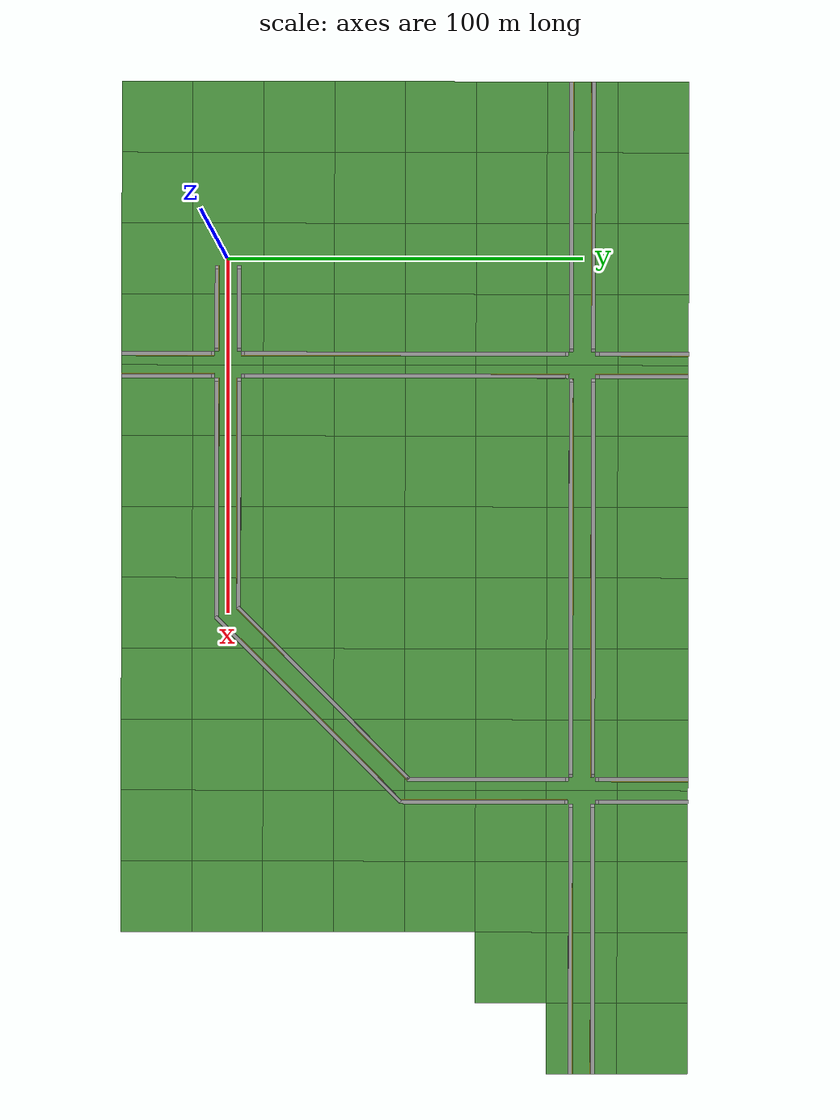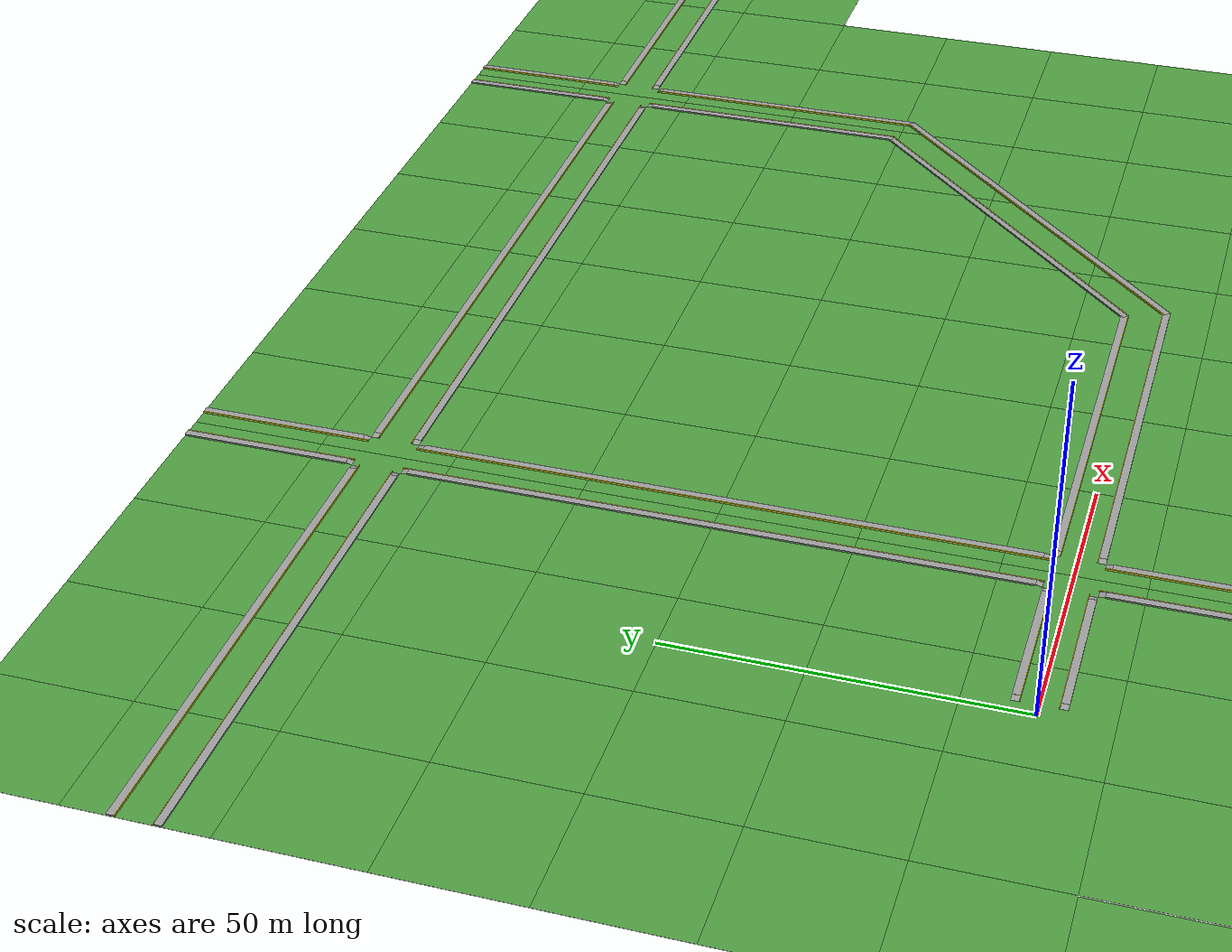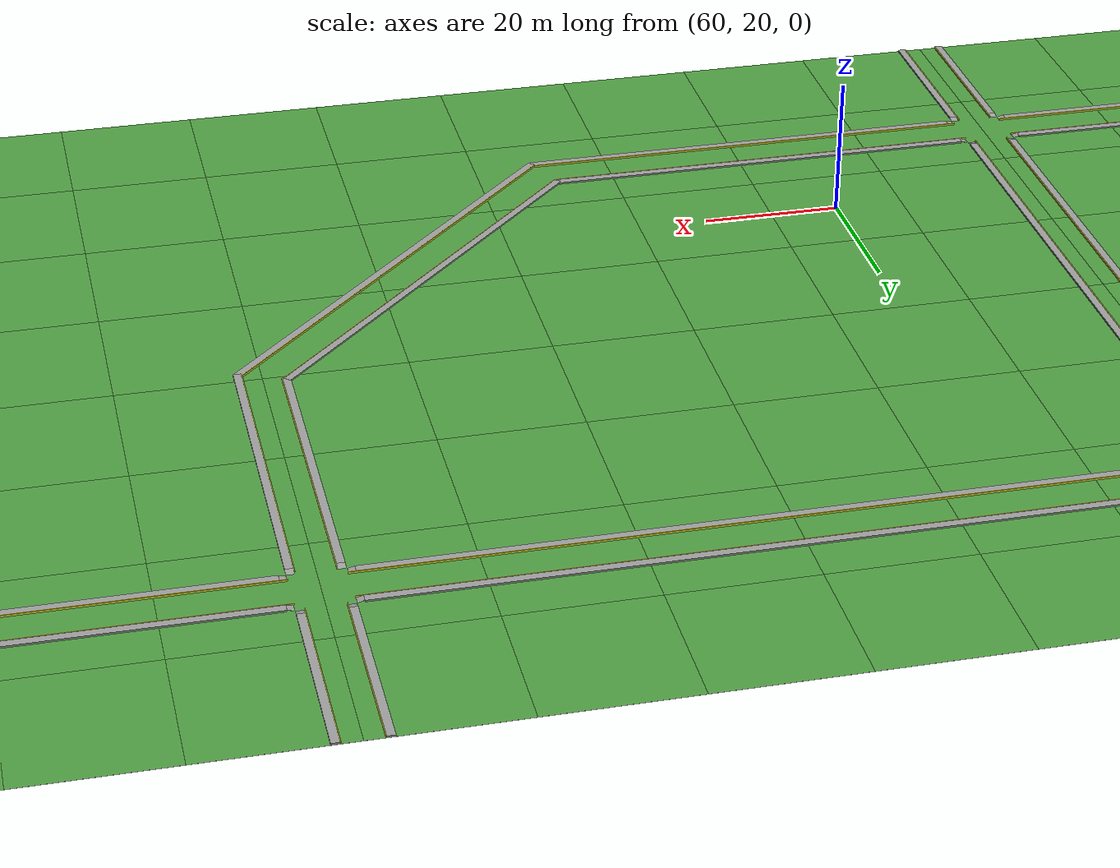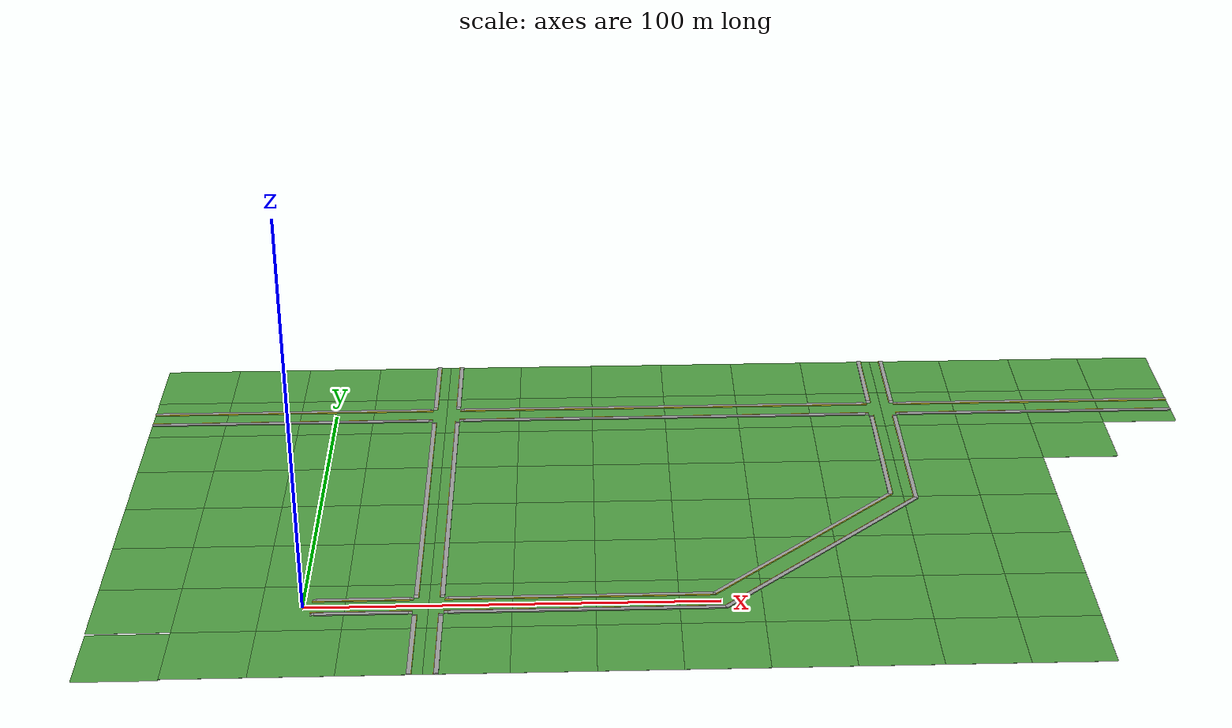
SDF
<sdf version="1.4">
 <world name="delivery_1">
  <scene><ambient>0.2 0.2 0.2 1.0</ambient><grid>false</grid></scene>
  <include><uri>model://grass_plane</uri></include>
  <include><uri>model://sun</uri></include>
  <model name="road_boxes_1">
   <static>true</static>
   <link name="link">
    <collision name="collision_1">
     <pose>51 0 0 0 0 0</pose>
     <geometry><box><size>102 7.4 0.02</size></box></geometry>
     <surface><friction><ode><mu>100</mu><mu2>50</mu2></ode></friction></surface>
    </collision>
    <collision name="collision_2">
     <pose>125 25 0 0 0 0.78539</pose>
     <geometry><box><size>72 7.4 0.02</size></box></geometry>
     <surface><friction><ode><mu>100</mu><mu2>50</mu2></ode></friction></surface>
    </collision>
    <collision name="collision_3">
     <pose>150 90 0 0 0 0</pose>
     <geometry><box><size>7.4 81.0 0.02</size></box></geometry>
     <surface><friction><ode><mu>100</mu><mu2>50</mu2></ode></friction></surface>
    </collision>
   </link>
  </model>
  <model name="road_boxes_2">
   <static>true</static>
   <link name="link">
    <collision name="collision_1">
     <pose>30 50 0 0 0 0</pose>
     <geometry><box><size>7.4 160 0.02</size></box></geometry>
     <surface><friction><ode><mu>100</mu><mu2>50</mu2></ode></friction></surface>
    </collision>
    <collision name="collision_2">
     <pose>90 100 0 0 0 0</pose>
     <geometry><box><size>120 7.4 0.02</size></box></geometry>
     <surface><friction><ode><mu>100</mu><mu2>50</mu2></ode></friction></surface>
    </collision>
   </link>
  </model>
  <model name="sidewalk_1">
   <static>true</static>
   <link name="sidewalk_1">
    <collision name="collision_ramp1a">
     <pose>2.5 -3.15 0.12 0 -0.262 0</pose>
     <geometry><box><size>1.033 1.1 0.01</size></box></geometry>
     <surface><friction><ode><mu>100</mu><mu2>50</mu2></ode></friction></surface>
    </collision>
    <visual name="visual_ramp1a">
     <pose>2.5 -3.15 0.12 0 -0.262 0</pose>
     <geometry><box><size>1.033 1.1 0.01</size></box></geometry>
     <material>
      <script><uri>file://media/materials/scripts/gazebo.material</uri><name>Gazebo/Grey</name></script>
     </material>
    </visual>
    <collision name="collision_ramp1b">
     <pose>2.5 3.15 0.12 0 -0.262 0</pose>
     <geometry><box><size>1.033 1.1 0.01</size></box></geometry>
     <surface><friction><ode><mu>100</mu><mu2>50</mu2></ode></friction></surface>
    </collision>
    <visual name="visual_ramp1b">
     <pose>2.5 3.15 0.12 0 -0.262 0</pose>
     <geometry><box><size>1.033 1.1 0.01</size></box></geometry>
     <material>
      <script><uri>file://media/materials/scripts/gazebo.material</uri><name>Gazebo/Grey</name></script>
     </material>
    </visual>
    <collision name="collision_ramp2a">
     <pose>25.8 -3.15 0.12 0 0.262 0</pose>
     <geometry><box><size>1.033 1.1 0.01</size></box></geometry>
     <surface><friction><ode><mu>100</mu><mu2>50</mu2></ode></friction></surface>
    </collision>
    <visual name="visual_ramp2a">
     <pose>25.8 -3.15 0.12 0 0.262 0</pose>
     <geometry><box><size>1.033 1.1 0.01</size></box></geometry>
     <material>
      <script><uri>file://media/materials/scripts/gazebo.material</uri><name>Gazebo/Grey</name></script>
     </material>
    </visual>
    <collision name="collision_ramp2b">
     <pose>25.8 3.15 0.12 0 0.262 0</pose>
     <geometry><box><size>1.033 1.1 0.01</size></box></geometry>
     <surface><friction><ode><mu>100</mu><mu2>50</mu2></ode></friction></surface>
    </collision>
    <visual name="visual_ramp2b">
     <pose>25.8 3.15 0.12 0 0.262 0</pose>
     <geometry><box><size>1.033 1.1 0.01</size></box></geometry>
     <material>
      <script><uri>file://media/materials/scripts/gazebo.material</uri><name>Gazebo/Grey</name></script>
     </material>
    </visual>
    <collision name="collision_ramp3a">
     <pose>34.2 3.15 0.12 0 -0.262 0</pose>
     <geometry><box><size>1.033 1.1 0.01</size></box></geometry>
     <surface><friction><ode><mu>100</mu><mu2>50</mu2></ode></friction></surface>
    </collision>
    <visual name="visual_ramp3a">
     <pose>34.2 3.15 0.12 0 -0.262 0</pose>
     <geometry><box><size>1.033 1.1 0.01</size></box></geometry>
     <material>
      <script><uri>file://media/materials/scripts/gazebo.material</uri><name>Gazebo/Grey</name></script>
     </material>
    </visual>
    <collision name="collision_ramp3b">
     <pose>34.2 -3.15 0.12 0 -0.262 0</pose>
     <geometry><box><size>1.033 1.1 0.01</size></box></geometry>
     <surface><friction><ode><mu>100</mu><mu2>50</mu2></ode></friction></surface>
    </collision>
    <visual name="visual_ramp3b">
     <pose>34.2 -3.15 0.12 0 -0.262 0</pose>
     <geometry><box><size>1.033 1.1 0.01</size></box></geometry>
     <material>
      <script><uri>file://media/materials/scripts/gazebo.material</uri><name>Gazebo/Grey</name></script>
     </material>
    </visual>
    <collision name="collision_ramp4a">
     <pose>146.85 95.80 0.12 -0.262 0 0</pose>
     <geometry><box><size>1.1 1.033 0.01</size></box></geometry>
     <surface><friction><ode><mu>100</mu><mu2>50</mu2></ode></friction></surface>
    </collision>
    <visual name="visual_ramp4a">
     <pose>146.85 95.80 0.12 -0.262 0 0</pose>
     <geometry><box><size>1.1 1.033 0.01</size></box></geometry>
     <material>
      <script><uri>file://media/materials/scripts/gazebo.material</uri><name>Gazebo/Grey</name></script>
     </material>
    </visual>
    <collision name="collision_ramp4b">
     <pose>153.21 95.71 0.12 -0.262 0 0</pose>
     <geometry><box><size>1.1 1.033 0.01</size></box></geometry>
     <surface><friction><ode><mu>100</mu><mu2>50</mu2></ode></friction></surface>
    </collision>
    <visual name="visual_ramp4b">
     <pose>153.21 95.72 0.12 -0.262 0 0</pose>
     <geometry><box><size>1.1 1.033 0.01</size></box></geometry>
     <material>
      <script><uri>file://media/materials/scripts/gazebo.material</uri><name>Gazebo/Grey</name></script>
     </material>
    </visual>
    <collision name="collision_ramp5a">
     <pose>146.85 104.2 0.12 0.262 0 0</pose>
     <geometry><box><size>1.1 1.033 0.01</size></box></geometry>
     <surface><friction><ode><mu>100</mu><mu2>50</mu2></ode></friction></surface>
    </collision>
    <visual name="visual_ramp5a">
     <pose>146.85 104.2 0.12 0.262 0 0</pose>
     <geometry><box><size>1.1 1.033 0.01</size></box></geometry>
     <material>
      <script><uri>file://media/materials/scripts/gazebo.material</uri><name>Gazebo/Grey</name></script>
     </material>
    </visual>
    <collision name="collision_ramp5b">
     <pose>153.21 104.2 0.12 0.262 0 0</pose>
     <geometry><box><size>1.1 1.033 0.01</size></box></geometry>
     <surface><friction><ode><mu>100</mu><mu2>50</mu2></ode></friction></surface>
    </collision>
    <visual name="visual_ramp5b">
     <pose>153.21 104.2 0.12 0.262 0 0</pose>
     <geometry><box><size>1.1 1.033 0.01</size></box></geometry>
     <material>
      <script><uri>file://media/materials/scripts/gazebo.material</uri><name>Gazebo/Grey</name></script>
     </material>
    </visual>
    <collision name="collision_sidewalk1a">
     <pose>14.15 -3.15 0.13 0 0 0</pose>
     <geometry><box><size>22.3 1.1 0.26</size></box></geometry>
     <surface><friction><ode><mu>100</mu><mu2>50</mu2></ode></friction></surface>
    </collision>
    <visual name="visual_sidewalk1a">
     <pose>14.15 -3.15 0.13 0 0 0</pose>
     <geometry><box><size>22.3 1.1 0.26</size></box></geometry>
     <material>
      <script><uri>file://media/materials/scripts/gazebo.material</uri><name>Gazebo/Grey</name></script>
     </material>
    </visual>
    <collision name="collision_sidewalk1b">
     <pose>14.15 3.15 0.13 0 0 0</pose>
     <geometry><box><size>22.3 1.1 0.26</size></box></geometry>
     <surface><friction><ode><mu>100</mu><mu2>50</mu2></ode></friction></surface>
    </collision>
    <visual name="visual_sidewalk1b">
     <pose>14.15 3.15 0.13 0 0 0</pose>
     <geometry><box><size>22.3 1.1 0.26</size></box></geometry>
     <material>
      <script><uri>file://media/materials/scripts/gazebo.material</uri><name>Gazebo/Grey</name></script>
     </material>
    </visual>
    <collision name="collision_sidewalk2a">
     <pose>68.12 -3.15 0.13 0 0 0</pose>
     <geometry><box><size>66.84 1.1 0.26</size></box></geometry>
     <surface><friction><ode><mu>100</mu><mu2>50</mu2></ode></friction></surface>
    </collision>
    <visual name="visual_sidewalk2a">
     <pose>68.12 -3.15 0.13 0 0 0</pose>
     <geometry><box><size>66.84 1.1 0.26</size></box></geometry>
     <material>
      <script><uri>file://media/materials/scripts/gazebo.material</uri><name>Gazebo/Grey</name></script>
     </material>
    </visual>
    <collision name="collision_sidewalk2b">
     <pose>66.73 3.15 0.13 0 0 0</pose>
     <geometry><box><size>64.07 1.1 0.26</size></box></geometry>
     <surface><friction><ode><mu>100</mu><mu2>50</mu2></ode></friction></surface>
    </collision>
    <visual name="visual_sidewalk2b">
     <pose>66.73 3.15 0.13 0 0 0</pose>
     <geometry><box><size>64.07 1.1 0.26</size></box></geometry>
     <material>
      <script><uri>file://media/materials/scripts/gazebo.material</uri><name>Gazebo/Grey</name></script>
     </material>
    </visual>
    <collision name="collision_sidewalk3a">
     <pose>127.2 22.8 0.13 0 0 0.785</pose>
     <geometry><box><size>73.8 1.1 0.26</size></box></geometry>
     <surface><friction><ode><mu>100</mu><mu2>50</mu2></ode></friction></surface>
    </collision>
    <visual name="visual_sidewalk3a">
     <pose>127.2 22.8 0.13 0 0 0.785</pose>
     <geometry><box><size>73.8 1.1 0.26</size></box></geometry>
     <material>
      <script><uri>file://media/materials/scripts/gazebo.material</uri><name>Gazebo/Grey</name></script>
     </material>
    </visual>
    <collision name="collision_sidewalk3b">
     <pose>122.6 27.05 0.13 0 0 0.785</pose>
     <geometry><box><size>68.35 1.1 0.26</size></box></geometry>
     <surface><friction><ode><mu>100</mu><mu2>50</mu2></ode></friction></surface>
    </collision>
    <visual name="visual_sidewalk3b">
     <pose>122.6 27.05 0.13 0 0 0.785</pose>
     <geometry><box><size>68.35 1.1 0.26</size></box></geometry>
     <material>
      <script><uri>file://media/materials/scripts/gazebo.material</uri><name>Gazebo/Grey</name></script>
     </material>
    </visual>
    <collision name="collision_sidewalk4a">
     <pose>146.85 73.05 0.13 0 0 0</pose>
     <geometry><box><size>1.1 44.5 0.26</size></box></geometry>
     <surface><friction><ode><mu>100</mu><mu2>50</mu2></ode></friction></surface>
    </collision>
    <visual name="visual_sidewalk4a">
     <pose>146.85 73.05 0.13 0 0 0.0</pose>
     <geometry><box><size>1.1 44.5 0.26</size></box></geometry>
     <material>
      <script><uri>file://media/materials/scripts/gazebo.material</uri><name>Gazebo/Grey</name></script>
     </material>
    </visual>
    <collision name="collision_sidewalk4b">
     <pose>153.21 71.86 0.13 0 0 0</pose>
     <geometry><box><size>1.1 46.72 0.26</size></box></geometry>
     <surface><friction><ode><mu>100</mu><mu2>50</mu2></ode></friction></surface>
    </collision>
    <visual name="visual_sidewalk4b">
     <pose>153.21 71.86 0.13 0 0 0.0</pose>
     <geometry><box><size>1.1 46.72 0.26</size></box></geometry>
     <material>
      <script><uri>file://media/materials/scripts/gazebo.material</uri><name>Gazebo/Grey</name></script>
     </material>
    </visual>
    <collision name="collision_sidewalk5a">
     <pose>146.85 117.35 0.13 0 0 0</pose>
     <geometry><box><size>1.1 25.3 0.26</size></box></geometry>
     <surface><friction><ode><mu>100</mu><mu2>50</mu2></ode></friction></surface>
    </collision>
    <visual name="visual_sidewalk5a">
     <pose>146.85 117.35 0.13 0 0 0.0</pose>
     <geometry><box><size>1.1 25.3 0.26</size></box></geometry>
     <material>
      <script><uri>file://media/materials/scripts/gazebo.material</uri><name>Gazebo/Grey</name></script>
     </material>
    </visual>
    <collision name="collision_sidewalk5b">
     <pose>153.21 117.35 0.13 0 0 0</pose>
     <geometry><box><size>1.1 25.3 0.26</size></box></geometry>
     <surface><friction><ode><mu>100</mu><mu2>50</mu2></ode></friction></surface>
    </collision>
    <visual name="visual_sidewalk5b">
     <pose>153.21 117.35 0.13 0 0 0.0</pose>
     <geometry><box><size>1.1 25.3 0.26</size></box></geometry>
     <material>
      <script><uri>file://media/materials/scripts/gazebo.material</uri><name>Gazebo/Grey</name></script>
     </material>
    </visual>
    <collision name="collision_curb1a">
     <pose>14.15 -2.55 0.15 0 0 0</pose>
     <geometry><box><size>24.3 0.1 0.3</size></box></geometry>
     <surface><friction><ode><mu>100</mu><mu2>50</mu2></ode></friction></surface>
    </collision>
    <visual name="visual_curb1a">
     <pose>14.15 -2.55 0.15 0 0 0</pose>
     <geometry><box><size>24.3 0.1 0.3</size></box></geometry>
     <material>
      <script><uri>file://media/materials/scripts/gazebo.material</uri><name>Gazebo/Yellow</name></script>
     </material>
    </visual>
    <collision name="collision_curb1b">
     <pose>14.15 2.55 0.15 0 0 0</pose>
     <geometry><box><size>24.3 0.1 0.3</size></box></geometry>
     <surface><friction><ode><mu>100</mu><mu2>50</mu2></ode></friction></surface>
    </collision>
    <visual name="visual_curb1b">
     <pose>14.15 2.55 0.15 0 0 0</pose>
     <geometry><box><size>24.3 0.1 0.3</size></box></geometry>
     <material>
      <script><uri>file://media/materials/scripts/gazebo.material</uri><name>Gazebo/Yellow</name></script>
     </material>
    </visual>
    <collision name="collision_curb2a">
     <pose>67.42 -2.55 0.15 0 0 0</pose>
     <geometry><box><size>67.44 0.1 0.3</size></box></geometry>
     <surface><friction><ode><mu>100</mu><mu2>50</mu2></ode></friction></surface>
    </collision>
    <visual name="visual_curb2a">
     <pose>67.42 -2.55 0.15 0 0 0</pose>
     <geometry><box><size>67.44 0.1 0.3</size></box></geometry>
     <material>
      <script><uri>file://media/materials/scripts/gazebo.material</uri><name>Gazebo/Yellow</name></script>
     </material>
    </visual>
    <collision name="collision_curb2b">
     <pose>66.23 2.55 0.15 0 0 0</pose>
     <geometry><box><size>65.07 0.1 0.3</size></box></geometry>
     <surface><friction><ode><mu>100</mu><mu2>50</mu2></ode></friction></surface>
    </collision>
    <visual name="visual_curb2b">
     <pose>66.23 2.55 0.15 0 0 0</pose>
     <geometry><box><size>65.07 0.1 0.3</size></box></geometry>
     <material>
      <script><uri>file://media/materials/scripts/gazebo.material</uri><name>Gazebo/Yellow</name></script>
     </material>
    </visual>
    <collision name="collision_curb3a">
     <pose>123.04 26.75 0.15 0 0 0.785</pose>
     <geometry><box><size>68.30 0.1 0.3</size></box></geometry>
     <surface><friction><ode><mu>100</mu><mu2>50</mu2></ode></friction></surface>
    </collision>
    <visual name="visual_curb3a">
     <pose>123.04 26.75 0.15 0 0 0.785</pose>
     <geometry><box><size>68.30 0.1 0.3</size></box></geometry>
     <material>
      <script><uri>file://media/materials/scripts/gazebo.material</uri><name>Gazebo/Yellow</name></script>
     </material>
    </visual>
    <collision name="collision_curb3b">
     <pose>126.75 23.27 0.15 0 0 0.785</pose>
     <geometry><box><size>73.424 0.1 0.3</size></box></geometry>
     <surface><friction><ode><mu>100</mu><mu2>50</mu2></ode></friction></surface>
    </collision>
    <visual name="visual_curb3b">
     <pose>126.75 23.27 0.15 0 0 0.785</pose>
     <geometry><box><size>73.424 0.1 0.3</size></box></geometry>
     <material>
      <script><uri>file://media/materials/scripts/gazebo.material</uri><name>Gazebo/Yellow</name></script>
     </material>
    </visual>
    <collision name="collision_curb4a">
     <pose>147.45 73.512 0.15 0 0 0</pose>
     <geometry><box><size>0.1 45.21 0.3</size></box></geometry>
     <surface><friction><ode><mu>100</mu><mu2>50</mu2></ode></friction></surface>
    </collision>
    <visual name="visual_curb4a">
     <pose>147.45 73.512 0.15 0 0 0</pose>
     <geometry><box><size>0.1 45.21 0.3</size></box></geometry>
     <material>
      <script><uri>file://media/materials/scripts/gazebo.material</uri><name>Gazebo/Yellow</name></script>
     </material>
    </visual>
    <collision name="collision_curb4b">
     <pose>152.61 72.527 0.15 0 0 0</pose>
     <geometry><box><size>0.1 46.624 0.3</size></box></geometry>
     <surface><friction><ode><mu>100</mu><mu2>50</mu2></ode></friction></surface>
    </collision>
    <visual name="visual_curb4b">
     <pose>152.61 72.527 0.15 0 0 0</pose>
     <geometry><box><size>0.1 46.624 0.3</size></box></geometry>
     <material>
      <script><uri>file://media/materials/scripts/gazebo.material</uri><name>Gazebo/Yellow</name></script>
     </material>
    </visual>
    <collision name="collision_curb5a">
     <pose>147.45 116.85 0.15 0 0 0</pose>
     <geometry><box><size>0.1 26.3 0.3</size></box></geometry>
     <surface><friction><ode><mu>100</mu><mu2>50</mu2></ode></friction></surface>
    </collision>
    <visual name="visual_curb5a">
     <pose>147.45 116.85 0.15 0 0 0</pose>
     <geometry><box><size>0.1 26.3 0.3</size></box></geometry>
     <material>
      <script><uri>file://media/materials/scripts/gazebo.material</uri><name>Gazebo/Yellow</name></script>
     </material>
    </visual>
    <collision name="collision_curb5b">
     <pose>152.61 116.85 0.15 0 0 0</pose>
     <geometry><box><size>0.1 26.3 0.3</size></box></geometry>
     <surface><friction><ode><mu>100</mu><mu2>50</mu2></ode></friction></surface>
    </collision>
    <visual name="visual_curb5b">
     <pose>152.61 116.85 0.15 0 0 0</pose>
     <geometry><box><size>0.1 26.3 0.3</size></box></geometry>
     <material>
      <script><uri>file://media/materials/scripts/gazebo.material</uri><name>Gazebo/Yellow</name></script>
     </material>
    </visual>
   </link>
  </model>
  <model name="sidewalk_2">
   <static>true</static>
   <link name="sidewalk_2">
    <collision name="collision_ramp1a">
     <pose>26.85 -4.2 0.12 -0.262 0 0</pose>
     <geometry><box><size>1.1 1.033 0.01</size></box></geometry>
     <surface><friction><ode><mu>100</mu><mu2>50</mu2></ode></friction></surface>
    </collision>
    <visual name="visual_ramp1a">
     <pose>26.85 -4.2 0.12 -0.262 0 0</pose>
     <geometry><box><size>1.1 1.033 0.01</size></box></geometry>
     <material>
      <script><uri>file://media/materials/scripts/gazebo.material</uri><name>Gazebo/Grey</name></script>
     </material>
    </visual>
    <collision name="collision_ramp1b">
     <pose>33.15 -4.2 0.12 -0.262 0 0</pose>
     <geometry><box><size>1.1 1.033 0.01</size></box></geometry>
     <surface><friction><ode><mu>100</mu><mu2>50</mu2></ode></friction></surface>
    </collision>
    <visual name="visual_ramp1b">
     <pose>33.15 -4.2 0.12 -0.262 0 0</pose>
     <geometry><box><size>1.1 1.033 0.01</size></box></geometry>
     <material>
      <script><uri>file://media/materials/scripts/gazebo.material</uri><name>Gazebo/Grey</name></script>
     </material>
    </visual>
    <collision name="collision_ramp2a">
     <pose>26.85 4.2 0.12 0.262 0 0</pose>
     <geometry><box><size>1.1 1.033 0.01</size></box></geometry>
     <surface><friction><ode><mu>100</mu><mu2>50</mu2></ode></friction></surface>
    </collision>
    <visual name="visual_ramp2a">
     <pose>26.85 4.2 0.12 0.262 0 0</pose>
     <geometry><box><size>1.1 1.033 0.01</size></box></geometry>
     <material>
      <script><uri>file://media/materials/scripts/gazebo.material</uri><name>Gazebo/Grey</name></script>
     </material>
    </visual>
    <collision name="collision_ramp2b">
     <pose>33.15 4.2 0.12 0.262 0 0</pose>
     <geometry><box><size>1.1 1.033 0.01</size></box></geometry>
     <surface><friction><ode><mu>100</mu><mu2>50</mu2></ode></friction></surface>
    </collision>
    <visual name="visual_ramp2b">
     <pose>33.15 4.2 0.12 0.262 0 0</pose>
     <geometry><box><size>1.1 1.033 0.01</size></box></geometry>
     <material>
      <script><uri>file://media/materials/scripts/gazebo.material</uri><name>Gazebo/Grey</name></script>
     </material>
    </visual>
    <collision name="collision_ramp3a">
     <pose>26.85 95.8 0.12 -0.262 0 0</pose>
     <geometry><box><size>1.1 1.033 0.01</size></box></geometry>
     <surface><friction><ode><mu>100</mu><mu2>50</mu2></ode></friction></surface>
    </collision>
    <visual name="visual_ramp3a">
     <pose>26.85 95.8 0.12 -0.262 0 0</pose>
     <geometry><box><size>1.1 1.033 0.01</size></box></geometry>
     <material>
      <script><uri>file://media/materials/scripts/gazebo.material</uri><name>Gazebo/Grey</name></script>
     </material>
    </visual>
    <collision name="collision_ramp3b">
     <pose>33.15 95.8 0.12 -0.262 0 0</pose>
     <geometry><box><size>1.1 1.033 0.01</size></box></geometry>
     <surface><friction><ode><mu>100</mu><mu2>50</mu2></ode></friction></surface>
    </collision>
    <visual name="visual_ramp3b">
     <pose>33.15 95.8 0.12 -0.262 0 0</pose>
     <geometry><box><size>1.1 1.033 0.01</size></box></geometry>
     <material>
      <script><uri>file://media/materials/scripts/gazebo.material</uri><name>Gazebo/Grey</name></script>
     </material>
    </visual>
    <collision name="collision_ramp4a">
     <pose>26.85 104.2 0.12 0.262 0 0</pose>
     <geometry><box><size>1.1 1.033 0.01</size></box></geometry>
     <surface><friction><ode><mu>100</mu><mu2>50</mu2></ode></friction></surface>
    </collision>
    <visual name="visual_ramp4a">
     <pose>26.85 104.2 0.12 0.262 0 0</pose>
     <geometry><box><size>1.1 1.033 0.01</size></box></geometry>
     <material>
      <script><uri>file://media/materials/scripts/gazebo.material</uri><name>Gazebo/Grey</name></script>
     </material>
    </visual>
    <collision name="collision_ramp4b">
     <pose>33.15 104.2 0.12 0.262 0 0</pose>
     <geometry><box><size>1.1 1.033 0.01</size></box></geometry>
     <surface><friction><ode><mu>100</mu><mu2>50</mu2></ode></friction></surface>
    </collision>
    <visual name="visual_ramp4b">
     <pose>33.15 104.2 0.12 0.262 0 0</pose>
     <geometry><box><size>1.1 1.033 0.01</size></box></geometry>
     <material>
      <script><uri>file://media/materials/scripts/gazebo.material</uri><name>Gazebo/Grey</name></script>
     </material>
    </visual>
    <collision name="collision_sidewalk1a">
     <pose>26.85 -17.35 0.13 0 0 0</pose>
     <geometry><box><size>1.1 25.3 0.26</size></box></geometry>
     <surface><friction><ode><mu>100</mu><mu2>50</mu2></ode></friction></surface>
    </collision>
    <visual name="visual_sidewalk1a">
     <pose>26.85 -17.35 0.13 0 0 0</pose>
     <geometry><box><size>1.1 25.3 0.26</size></box></geometry>
     <material>
      <script><uri>file://media/materials/scripts/gazebo.material</uri><name>Gazebo/Grey</name></script>
     </material>
    </visual>
    <collision name="collision_sidewalk1b">
     <pose>33.15 -17.35 0.13 0 0 0</pose>
     <geometry><box><size>1.1 25.3 0.26</size></box></geometry>
     <surface><friction><ode><mu>100</mu><mu2>50</mu2></ode></friction></surface>
    </collision>
    <visual name="visual_sidewalk1b">
     <pose>33.15 -17.35 0.13 0 0 0</pose>
     <geometry><box><size>1.1 25.3 0.26</size></box></geometry>
     <material>
      <script><uri>file://media/materials/scripts/gazebo.material</uri><name>Gazebo/Grey</name></script>
     </material>
    </visual>
    <collision name="collision_sidewalk2a">
     <pose>26.85 50 0.13 0 0 0</pose>
     <geometry><box><size>1.1 90.6 0.26</size></box></geometry>
     <surface><friction><ode><mu>100</mu><mu2>50</mu2></ode></friction></surface>
    </collision>
    <visual name="visual_sidewalk2a">
     <pose>26.85 50 0.13 0 0 0</pose>
     <geometry><box><size>1.1 90.6 0.26</size></box></geometry>
     <material>
      <script><uri>file://media/materials/scripts/gazebo.material</uri><name>Gazebo/Grey</name></script>
     </material>
    </visual>
    <collision name="collision_sidewalk2b">
     <pose>33.15 50 0.13 0 0 0</pose>
     <geometry><box><size>1.1 90.6 0.26</size></box></geometry>
     <surface><friction><ode><mu>100</mu><mu2>50</mu2></ode></friction></surface>
    </collision>
    <visual name="visual_sidewalk2b">
     <pose>33.15 50 0.13 0 0 0</pose>
     <geometry><box><size>1.1 90.6 0.26</size></box></geometry>
     <material>
      <script><uri>file://media/materials/scripts/gazebo.material</uri><name>Gazebo/Grey</name></script>
     </material>
    </visual>
    <collision name="collision_sidewalk3a">
     <pose>26.85 117.35 0.13 0 0 0</pose>
     <geometry><box><size>1.1 25.3 0.26</size></box></geometry>
     <surface><friction><ode><mu>100</mu><mu2>50</mu2></ode></friction></surface>
    </collision>
    <visual name="visual_sidewalk3a">
     <pose>26.85 117.35 0.13 0 0 0</pose>
     <geometry><box><size>1.1 25.3 0.26</size></box></geometry>
     <material>
      <script><uri>file://media/materials/scripts/gazebo.material</uri><name>Gazebo/Grey</name></script>
     </material>
    </visual>
    <collision name="collision_sidewalk3b">
     <pose>33.15 117.35 0.13 0 0 0</pose>
     <geometry><box><size>1.1 25.3 0.26</size></box></geometry>
     <surface><friction><ode><mu>100</mu><mu2>50</mu2></ode></friction></surface>
    </collision>
    <visual name="visual_sidewalk3b">
     <pose>33.15 117.35 0.13 0 0 0</pose>
     <geometry><box><size>1.1 25.3 0.26</size></box></geometry>
     <material>
      <script><uri>file://media/materials/scripts/gazebo.material</uri><name>Gazebo/Grey</name></script>
     </material>
    </visual>
    <collision name="collision_curb1a">
     <pose>27.45 -16.85 0.15 0 0 0</pose>
     <geometry><box><size>0.1 26.3 0.3</size></box></geometry>
     <surface><friction><ode><mu>100</mu><mu2>50</mu2></ode></friction></surface>
    </collision>
    <visual name="visual_curb1a">
     <pose>27.45 -16.85 0.15 0 0 0</pose>
     <geometry><box><size>0.1 26.3 0.3</size></box></geometry>
     <material>
      <script><uri>file://media/materials/scripts/gazebo.material</uri><name>Gazebo/Yellow</name></script>
     </material>
    </visual>
    <collision name="collision_curb1b">
     <pose>32.55 -16.85 0.15 0 0 0</pose>
     <geometry><box><size>0.1 26.3 0.3</size></box></geometry>
     <surface><friction><ode><mu>100</mu><mu2>50</mu2></ode></friction></surface>
    </collision>
    <visual name="visual_curb1b">
     <pose>32.55 -16.85 0.15 0 0 0</pose>
     <geometry><box><size>0.1 26.3 0.3</size></box></geometry>
     <material>
      <script><uri>file://media/materials/scripts/gazebo.material</uri><name>Gazebo/Yellow</name></script>
     </material>
    </visual>
    <collision name="collision_curb2a">
     <pose>27.45 50 0.15 0 0 0</pose>
     <geometry><box><size>0.1 92.6 0.3</size></box></geometry>
     <surface><friction><ode><mu>100</mu><mu2>50</mu2></ode></friction></surface>
    </collision>
    <visual name="visual_curb2a">
     <pose>27.45 50 0.15 0 0 0</pose>
     <geometry><box><size>0.1 92.6 0.3</size></box></geometry>
     <material>
      <script><uri>file://media/materials/scripts/gazebo.material</uri><name>Gazebo/Yellow</name></script>
     </material>
    </visual>
    <collision name="collision_curb2b">
     <pose>32.55 50 0.15 0 0 0</pose>
     <geometry><box><size>0.1 92.6 0.3</size></box></geometry>
     <surface><friction><ode><mu>100</mu><mu2>50</mu2></ode></friction></surface>
    </collision>
    <visual name="visual_curb2b">
     <pose>32.55 50 0.15 0 0 0</pose>
     <geometry><box><size>0.1 92.6 0.3</size></box></geometry>
     <material>
      <script><uri>file://media/materials/scripts/gazebo.material</uri><name>Gazebo/Yellow</name></script>
     </material>
    </visual>
    <collision name="collision_curb3a">
     <pose>27.45 116.85 0.15 0 0 0</pose>
     <geometry><box><size>0.1 26.3 0.3</size></box></geometry>
     <surface><friction><ode><mu>100</mu><mu2>50</mu2></ode></friction></surface>
    </collision>
    <visual name="visual_curb3a">
     <pose>27.45 116.85 0.15 0 0 0</pose>
     <geometry><box><size>0.1 26.3 0.3</size></box></geometry>
     <material>
      <script><uri>file://media/materials/scripts/gazebo.material</uri><name>Gazebo/Yellow</name></script>
     </material>
    </visual>
    <collision name="collision_curb3b">
     <pose>32.55 116.85 0.15 0 0 0</pose>
     <geometry><box><size>0.1 26.3 0.3</size></box></geometry>
     <surface><friction><ode><mu>100</mu><mu2>50</mu2></ode></friction></surface>
    </collision>
    <visual name="visual_curb3b">
     <pose>32.55 116.85 0.15 0 0 0</pose>
     <geometry><box><size>0.1 26.3 0.3</size></box></geometry>
     <material>
      <script><uri>file://media/materials/scripts/gazebo.material</uri><name>Gazebo/Yellow</name></script>
     </material>
    </visual>
   </link>
  </model>
  <model name="sidewalk_3">
   <static>true</static>
   <link name="sidewalk_3">
    <collision name="collision_ramp1a">
     <pose>25.8 96.85 0.12 0 0.262 0</pose>
     <geometry><box><size>1.033 1.1 0.01</size></box></geometry>
     <surface><friction><ode><mu>100</mu><mu2>50</mu2></ode></friction></surface>
    </collision>
    <visual name="visual_ramp1a">
     <pose>25.8 96.85 0.12 0 0.262 0</pose>
     <geometry><box><size>1.033 1.1 0.01</size></box></geometry>
     <material>
      <script><uri>file://media/materials/scripts/gazebo.material</uri><name>Gazebo/Grey</name></script>
     </material>
    </visual>
    <collision name="collision_ramp1b">
     <pose>25.8 103.15 0.12 0 0.262 0</pose>
     <geometry><box><size>1.033 1.1 0.01</size></box></geometry>
     <surface><friction><ode><mu>100</mu><mu2>50</mu2></ode></friction></surface>
    </collision>
    <visual name="visual_ramp1b">
     <pose>25.8 103.15 0.12 0 0.262 0</pose>
     <geometry><box><size>1.033 1.1 0.01</size></box></geometry>
     <material>
      <script><uri>file://media/materials/scripts/gazebo.material</uri><name>Gazebo/Grey</name></script>
     </material>
    </visual>
    <collision name="collision_ramp2a">
     <pose>34.2 96.85 0.12 0 -0.262 0</pose>
     <geometry><box><size>1.033 1.1 0.01</size></box></geometry>
     <surface><friction><ode><mu>100</mu><mu2>50</mu2></ode></friction></surface>
    </collision>
    <visual name="visual_ramp2a">
     <pose>34.2 96.85 0.12 0 -0.262 0</pose>
     <geometry><box><size>1.033 1.1 0.01</size></box></geometry>
     <material>
      <script><uri>file://media/materials/scripts/gazebo.material</uri><name>Gazebo/Grey</name></script>
     </material>
    </visual>
    <collision name="collision_ramp2b">
     <pose>34.2 103.15 0.12 0 -0.262 0</pose>
     <geometry><box><size>1.033 1.1 0.01</size></box></geometry>
     <surface><friction><ode><mu>100</mu><mu2>50</mu2></ode></friction></surface>
    </collision>
    <visual name="visual_ramp2b">
     <pose>34.2 103.15 0.12 0 -0.262 0</pose>
     <geometry><box><size>1.033 1.1 0.01</size></box></geometry>
     <material>
      <script><uri>file://media/materials/scripts/gazebo.material</uri><name>Gazebo/Grey</name></script>
     </material>
    </visual>
    <collision name="collision_ramp3a">
     <pose>145.8 96.85 0.12 0 0.262 0</pose>
     <geometry><box><size>1.033 1.1 0.01</size></box></geometry>
     <surface><friction><ode><mu>100</mu><mu2>50</mu2></ode></friction></surface>
    </collision>
    <visual name="visual_ramp3a">
     <pose>145.8 96.85 0.12 0 0.262 0</pose>
     <geometry><box><size>1.033 1.1 0.01</size></box></geometry>
     <material>
      <script><uri>file://media/materials/scripts/gazebo.material</uri><name>Gazebo/Grey</name></script>
     </material>
    </visual>
    <collision name="collision_ramp3b">
     <pose>145.8 103.15 0.12 0 0.262 0</pose>
     <geometry><box><size>1.033 1.1 0.01</size></box></geometry>
     <surface><friction><ode><mu>100</mu><mu2>50</mu2></ode></friction></surface>
    </collision>
    <visual name="visual_ramp3b">
     <pose>145.8 103.15 0.12 0 0.262 0</pose>
     <geometry><box><size>1.033 1.1 0.01</size></box></geometry>
     <material>
      <script><uri>file://media/materials/scripts/gazebo.material</uri><name>Gazebo/Grey</name></script>
     </material>
    </visual>
    <collision name="collision_ramp4a">
     <pose>154.2 96.85 0.12 0 -0.262 0</pose>
     <geometry><box><size>1.033 1.1 0.01</size></box></geometry>
     <surface><friction><ode><mu>100</mu><mu2>50</mu2></ode></friction></surface>
    </collision>
    <visual name="visual_ramp4a">
     <pose>154.2 96.85 0.12 0 -0.262 0</pose>
     <geometry><box><size>1.033 1.1 0.01</size></box></geometry>
     <material>
      <script><uri>file://media/materials/scripts/gazebo.material</uri><name>Gazebo/Grey</name></script>
     </material>
    </visual>
    <collision name="collision_ramp4b">
     <pose>154.2 103.15 0.12 0 -0.262 0</pose>
     <geometry><box><size>1.033 1.1 0.01</size></box></geometry>
     <surface><friction><ode><mu>100</mu><mu2>50</mu2></ode></friction></surface>
    </collision>
    <visual name="visual_ramp4b">
     <pose>154.2 103.15 0.12 0 -0.262 0</pose>
     <geometry><box><size>1.033 1.1 0.01</size></box></geometry>
     <material>
      <script><uri>file://media/materials/scripts/gazebo.material</uri><name>Gazebo/Grey</name></script>
     </material>
    </visual>
    <collision name="collision_sidewalk1a">
     <pose>-12.35 96.85 0.13 0 0 0</pose>
     <geometry><box><size>75.3 1.1 0.26</size></box></geometry>
     <surface><friction><ode><mu>100</mu><mu2>50</mu2></ode></friction></surface>
    </collision>
    <visual name="visual_sidewalk1a">
     <pose>-12.35 96.85 0.13 0 0 0</pose>
     <geometry><box><size>75.3 1.1 0.26</size></box></geometry>
     <material>
      <script><uri>file://media/materials/scripts/gazebo.material</uri><name>Gazebo/Grey</name></script>
     </material>
    </visual>
    <collision name="collision_sidewalk1b">
     <pose>-12.35 103.15 0.13 0 0 0</pose>
     <geometry><box><size>75.3 1.1 0.26</size></box></geometry>
     <surface><friction><ode><mu>100</mu><mu2>50</mu2></ode></friction></surface>
    </collision>
    <visual name="visual_sidewalk1b">
     <pose>-12.35 103.15 0.13 0 0 0</pose>
     <geometry><box><size>75.3 1.1 0.26</size></box></geometry>
     <material>
      <script><uri>file://media/materials/scripts/gazebo.material</uri><name>Gazebo/Grey</name></script>
     </material>
    </visual>
    <collision name="collision_sidewalk2a">
     <pose>90 96.85 0.13 0 0 0</pose>
     <geometry><box><size>110.6 1.1 0.26</size></box></geometry>
     <surface><friction><ode><mu>100</mu><mu2>50</mu2></ode></friction></surface>
    </collision>
    <visual name="visual_sidewalk2a">
     <pose>90 96.85 0.13 0 0 0</pose>
     <geometry><box><size>110.6 1.1 0.26</size></box></geometry>
     <material>
      <script><uri>file://media/materials/scripts/gazebo.material</uri><name>Gazebo/Grey</name></script>
     </material>
    </visual>
    <collision name="collision_sidewalk2b">
     <pose>90 103.15 0.13 0 0 0</pose>
     <geometry><box><size>110.6 1.1 0.26</size></box></geometry>
     <surface><friction><ode><mu>100</mu><mu2>50</mu2></ode></friction></surface>
    </collision>
    <visual name="visual_sidewalk2b">
     <pose>90 103.15 0.13 0 0 0</pose>
     <geometry><box><size>110.6 1.1 0.26</size></box></geometry>
     <material>
      <script><uri>file://media/materials/scripts/gazebo.material</uri><name>Gazebo/Grey</name></script>
     </material>
    </visual>
    <collision name="collision_sidewalk3a">
     <pose>192.35 96.85 0.13 0 0 0</pose>
     <geometry><box><size>75.3 1.1 0.26</size></box></geometry>
     <surface><friction><ode><mu>100</mu><mu2>50</mu2></ode></friction></surface>
    </collision>
    <visual name="visual_sidewalk3a">
     <pose>192.35 96.85 0.13 0 0 0</pose>
     <geometry><box><size>75.3 1.1 0.26</size></box></geometry>
     <material>
      <script><uri>file://media/materials/scripts/gazebo.material</uri><name>Gazebo/Grey</name></script>
     </material>
    </visual>
    <collision name="collision_sidewalk3b">
     <pose>192.35 103.15 0.13 0 0 0</pose>
     <geometry><box><size>75.3 1.1 0.26</size></box></geometry>
     <surface><friction><ode><mu>100</mu><mu2>50</mu2></ode></friction></surface>
    </collision>
    <visual name="visual_sidewalk3b">
     <pose>192.35 103.15 0.13 0 0 0</pose>
     <geometry><box><size>75.3 1.1 0.26</size></box></geometry>
     <material>
      <script><uri>file://media/materials/scripts/gazebo.material</uri><name>Gazebo/Grey</name></script>
     </material>
    </visual>
    <collision name="collision_curb1a">
     <pose>-11.85 97.45 0.15 0 0 0</pose>
     <geometry><box><size>76.3 0.1 0.3</size></box></geometry>
     <surface><friction><ode><mu>100</mu><mu2>50</mu2></ode></friction></surface>
    </collision>
    <visual name="visual_curb1a">
     <pose>-11.85 97.45 0.15 0 0 0</pose>
     <geometry><box><size>76.3 0.1 0.3</size></box></geometry>
     <material>
      <script><uri>file://media/materials/scripts/gazebo.material</uri><name>Gazebo/Yellow</name></script>
     </material>
    </visual>
    <collision name="collision_curb1b">
     <pose>-11.85 102.55 0.15 0 0 0</pose>
     <geometry><box><size>76.3 0.1 0.3</size></box></geometry>
     <surface><friction><ode><mu>100</mu><mu2>50</mu2></ode></friction></surface>
    </collision>
    <visual name="visual_curb1b">
     <pose>-11.85 102.55 0.15 0 0 0</pose>
     <geometry><box><size>76.3 0.1 0.3</size></box></geometry>
     <material>
      <script><uri>file://media/materials/scripts/gazebo.material</uri><name>Gazebo/Yellow</name></script>
     </material>
    </visual>
    <collision name="collision_curb2a">
     <pose>90 97.45 0.15 0 0 0</pose>
     <geometry><box><size>112.6 0.1 0.3</size></box></geometry>
     <surface><friction><ode><mu>100</mu><mu2>50</mu2></ode></friction></surface>
    </collision>
    <visual name="visual_curb2a">
     <pose>90 97.45 0.15 0 0 0</pose>
     <geometry><box><size>112.6 0.1 0.3</size></box></geometry>
     <material>
      <script><uri>file://media/materials/scripts/gazebo.material</uri><name>Gazebo/Yellow</name></script>
     </material>
    </visual>
    <collision name="collision_curb2b">
     <pose>90 102.55 0.15 0 0 0</pose>
     <geometry><box><size>112.6 0.1 0.3</size></box></geometry>
     <surface><friction><ode><mu>100</mu><mu2>50</mu2></ode></friction></surface>
    </collision>
    <visual name="visual_curb2b">
     <pose>90 102.55 0.15 0 0 0</pose>
     <geometry><box><size>112.6 0.1 0.3</size></box></geometry>
     <material>
      <script><uri>file://media/materials/scripts/gazebo.material</uri><name>Gazebo/Yellow</name></script>
     </material>
    </visual>
    <collision name="collision_curb3a">
     <pose>191.85 97.45 0.15 0 0 0</pose>
     <geometry><box><size>76.3 0.1 0.3</size></box></geometry>
     <surface><friction><ode><mu>100</mu><mu2>50</mu2></ode></friction></surface>
    </collision>
    <visual name="visual_curb3a">
     <pose>191.85 97.45 0.15 0 0 0</pose>
     <geometry><box><size>76.3 0.1 0.3</size></box></geometry>
     <material>
      <script><uri>file://media/materials/scripts/gazebo.material</uri><name>Gazebo/Yellow</name></script>
     </material>
    </visual>
    <collision name="collision_curb3b">
     <pose>191.85 102.55 0.15 0 0 0</pose>
     <geometry><box><size>76.3 0.1 0.3</size></box></geometry>
     <surface><friction><ode><mu>100</mu><mu2>50</mu2></ode></friction></surface>
    </collision>
    <visual name="visual_curb3b">
     <pose>191.85 102.55 0.15 0 0 0</pose>
     <geometry><box><size>76.3 0.1 0.3</size></box></geometry>
     <material>
      <script><uri>file://media/materials/scripts/gazebo.material</uri><name>Gazebo/Yellow</name></script>
     </material>
    </visual>
   </link>
  </model>
  <plugin filename="libcollision_map_creator.so" name="collision_map_creator"/>
 </world>
</sdf>

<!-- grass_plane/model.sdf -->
<sdf version='1.4'>
  <model name='grass_plane'>
    <static>true</static>
    <link name='link'>
      <collision name='collision'>
        <geometry>
          <plane>
            <normal>0 0 1</normal>
            <size>500 500</size>
          </plane>
        </geometry>
        <surface>
          <friction>
            <ode>
              <mu>0.5</mu>
              <mu2>.5</mu2>
            </ode>
          </friction>
        </surface>
      </collision>

      <visual name='visual_6'>
        <pose>-40 -20 0 0 0 0</pose>

        <cast_shadows>false</cast_shadows>
        <geometry>
          <plane>
            <normal>0 0 1</normal>
            <size>20 20</size>
          </plane>
        </geometry>
        <material>
          <script>
            <uri>model://grass_plane/materials/scripts</uri>
            <uri>model://grass_plane/materials/textures</uri>
            <name>vrc/grass</name>
          </script>
        </material>
      </visual>

      <visual name='visual_7'>
        <pose>-20 -20 0 0 0 0</pose>

        <cast_shadows>false</cast_shadows>
        <geometry>
          <plane>
            <normal>0 0 1</normal>
            <size>20 20</size>
          </plane>
        </geometry>
        <material>
          <script>
            <uri>model://grass_plane/materials/scripts</uri>
            <uri>model://grass_plane/materials/textures</uri>
            <name>vrc/grass</name>
          </script>
        </material>
      </visual>

      <visual name='visual_8'>
        <pose>0 -20 0 0 0 0</pose>

        <cast_shadows>false</cast_shadows>
        <geometry>
          <plane>
            <normal>0 0 1</normal>
            <size>20 20</size>
          </plane>
        </geometry>
        <material>
          <script>
            <uri>model://grass_plane/materials/scripts</uri>
            <uri>model://grass_plane/materials/textures</uri>
            <name>vrc/grass</name>
          </script>
        </material>
      </visual>

      <visual name='visual_9'>
        <pose>20 -20 0 0 0 0</pose>

        <cast_shadows>false</cast_shadows>
        <geometry>
          <plane>
            <normal>0 0 1</normal>
            <size>20 20</size>
          </plane>
        </geometry>
        <material>
          <script>
            <uri>model://grass_plane/materials/scripts</uri>
            <uri>model://grass_plane/materials/textures</uri>
            <name>vrc/grass</name>
          </script>
        </material>
      </visual>

      <visual name='visual_10'>
        <pose>40 -20 0 0 0 0</pose>

        <cast_shadows>false</cast_shadows>
        <geometry>
          <plane>
            <normal>0 0 1</normal>
            <size>20 20</size>
          </plane>
        </geometry>
        <material>
          <script>
            <uri>model://grass_plane/materials/scripts</uri>
            <uri>model://grass_plane/materials/textures</uri>
            <name>vrc/grass</name>
          </script>
        </material>
      </visual>

      <visual name='visual_11'>
        <pose>60 -20 0 0 0 0</pose>

        <cast_shadows>false</cast_shadows>
        <geometry>
          <plane>
            <normal>0 0 1</normal>
            <size>20 20</size>
          </plane>
        </geometry>
        <material>
          <script>
            <uri>model://grass_plane/materials/scripts</uri>
            <uri>model://grass_plane/materials/textures</uri>
            <name>vrc/grass</name>
          </script>
        </material>
      </visual>

      <visual name='visual_12'>
        <pose>80 -20 0 0 0 0</pose>

        <cast_shadows>false</cast_shadows>
        <geometry>
          <plane>
            <normal>0 0 1</normal>
            <size>20 20</size>
          </plane>
        </geometry>
        <material>
          <script>
            <uri>model://grass_plane/materials/scripts</uri>
            <uri>model://grass_plane/materials/textures</uri>
            <name>vrc/grass</name>
          </script>
        </material>
      </visual>

      <visual name='visual_12_1'>
        <pose>100 -20 0 0 0 0</pose>

        <cast_shadows>false</cast_shadows>
        <geometry>
          <plane>
            <normal>0 0 1</normal>
            <size>20 20</size>
          </plane>
        </geometry>
        <material>
          <script>
            <uri>model://grass_plane/materials/scripts</uri>
            <uri>model://grass_plane/materials/textures</uri>
            <name>vrc/grass</name>
          </script>
        </material>
      </visual>

      <visual name='visual_12_2'>
        <pose>120 -20 0 0 0 0</pose>

        <cast_shadows>false</cast_shadows>
        <geometry>
          <plane>
            <normal>0 0 1</normal>
            <size>20 20</size>
          </plane>
        </geometry>
        <material>
          <script>
            <uri>model://grass_plane/materials/scripts</uri>
            <uri>model://grass_plane/materials/textures</uri>
            <name>vrc/grass</name>
          </script>
        </material>
      </visual>

      <visual name='visual_12_3'>
        <pose>140 -20 0 0 0 0</pose>

        <cast_shadows>false</cast_shadows>
        <geometry>
          <plane>
            <normal>0 0 1</normal>
            <size>20 20</size>
          </plane>
        </geometry>
        <material>
          <script>
            <uri>model://grass_plane/materials/scripts</uri>
            <uri>model://grass_plane/materials/textures</uri>
            <name>vrc/grass</name>
          </script>
        </material>
      </visual>

      <visual name='visual_12_4'>
        <pose>160 -20 0 0 0 0</pose>

        <cast_shadows>false</cast_shadows>
        <geometry>
          <plane>
            <normal>0 0 1</normal>
            <size>20 20</size>
          </plane>
        </geometry>
        <material>
          <script>
            <uri>model://grass_plane/materials/scripts</uri>
            <uri>model://grass_plane/materials/textures</uri>
            <name>vrc/grass</name>
          </script>
        </material>
      </visual>

      <visual name='visual_12_5'>
        <pose>180 -20 0 0 0 0</pose>

        <cast_shadows>false</cast_shadows>
        <geometry>
          <plane>
            <normal>0 0 1</normal>
            <size>20 20</size>
          </plane>
        </geometry>
        <material>
          <script>
            <uri>model://grass_plane/materials/scripts</uri>
            <uri>model://grass_plane/materials/textures</uri>
            <name>vrc/grass</name>
          </script>
        </material>
      </visual>

      <visual name='visual_13'>
        <pose>-40 0 0 0 0 0</pose>

        <cast_shadows>false</cast_shadows>
        <geometry>
          <plane>
            <normal>0 0 1</normal>
            <size>20 20</size>
          </plane>
        </geometry>
        <material>
          <script>
            <uri>model://grass_plane/materials/scripts</uri>
            <uri>model://grass_plane/materials/textures</uri>
            <name>vrc/grass</name>
          </script>
        </material>
      </visual>

      <visual name='visual_14'>
        <pose>-20 0 0 0 0 0</pose>

        <cast_shadows>false</cast_shadows>
        <geometry>
          <plane>
            <normal>0 0 1</normal>
            <size>20 20</size>
          </plane>
        </geometry>
        <material>
          <script>
            <uri>model://grass_plane/materials/scripts</uri>
            <uri>model://grass_plane/materials/textures</uri>
            <name>vrc/grass</name>
          </script>
        </material>
      </visual>

      <visual name='visual_15'>
        <pose>0 0 0 0 0 0</pose>

        <cast_shadows>false</cast_shadows>
        <geometry>
          <plane>
            <normal>0 0 1</normal>
            <size>20 20</size>
          </plane>
        </geometry>
        <material>
          <script>
            <uri>model://grass_plane/materials/scripts</uri>
            <uri>model://grass_plane/materials/textures</uri>
            <name>vrc/grass</name>
          </script>
        </material>
      </visual>

      <visual name='visual_16'>
        <pose>20 0 0 0 0 0</pose>

        <cast_shadows>false</cast_shadows>
        <geometry>
          <plane>
            <normal>0 0 1</normal>
            <size>20 20</size>
          </plane>
        </geometry>
        <material>
          <script>
            <uri>model://grass_plane/materials/scripts</uri>
            <uri>model://grass_plane/materials/textures</uri>
            <name>vrc/grass</name>
          </script>
        </material>
      </visual>

      <visual name='visual_17'>
        <pose>40 0 0 0 0 0</pose>

        <cast_shadows>false</cast_shadows>
        <geometry>
          <plane>
            <normal>0 0 1</normal>
            <size>20 20</size>
          </plane>
        </geometry>
        <material>
          <script>
            <uri>model://grass_plane/materials/scripts</uri>
            <uri>model://grass_plane/materials/textures</uri>
            <name>vrc/grass</name>
          </script>
        </material>
      </visual>

      <visual name='visual_18'>
        <pose>60 0 0 0 0 0</pose>

        <cast_shadows>false</cast_shadows>
        <geometry>
          <plane>
            <normal>0 0 1</normal>
            <size>20 20</size>
          </plane>
        </geometry>
        <material>
          <script>
            <uri>model://grass_plane/materials/scripts</uri>
            <uri>model://grass_plane/materials/textures</uri>
            <name>vrc/grass</name>
          </script>
        </material>
      </visual>

      <visual name='visual_19'>
        <pose>80 0 0 0 0 0</pose>

        <cast_shadows>false</cast_shadows>
        <geometry>
          <plane>
            <normal>0 0 1</normal>
            <size>20 20</size>
          </plane>
        </geometry>
        <material>
          <script>
            <uri>model://grass_plane/materials/scripts</uri>
            <uri>model://grass_plane/materials/textures</uri>
            <name>vrc/grass</name>
          </script>
        </material>
      </visual>

      <visual name='visual_20'>
        <pose>100 0 0 0 0 0</pose>

        <cast_shadows>false</cast_shadows>
        <geometry>
          <plane>
            <normal>0 0 1</normal>
            <size>20 20</size>
          </plane>
        </geometry>
        <material>
          <script>
            <uri>model://grass_plane/materials/scripts</uri>
            <uri>model://grass_plane/materials/textures</uri>
            <name>vrc/grass</name>
          </script>
        </material>
      </visual>

      <visual name='visual_21'>
        <pose>120 0 0 0 0 0</pose>

        <cast_shadows>false</cast_shadows>
        <geometry>
          <plane>
            <normal>0 0 1</normal>
            <size>20 20</size>
          </plane>
        </geometry>
        <material>
          <script>
            <uri>model://grass_plane/materials/scripts</uri>
            <uri>model://grass_plane/materials/textures</uri>
            <name>vrc/grass</name>
          </script>
        </material>
      </visual>

      <visual name='visual_21_2'>
        <pose>140 0 0 0 0 0</pose>

        <cast_shadows>false</cast_shadows>
        <geometry>
          <plane>
            <normal>0 0 1</normal>
            <size>20 20</size>
          </plane>
        </geometry>
        <material>
          <script>
            <uri>model://grass_plane/materials/scripts</uri>
            <uri>model://grass_plane/materials/textures</uri>
            <name>vrc/grass</name>
          </script>
        </material>
      </visual>

      <visual name='visual_21_3'>
        <pose>160 0 0 0 0 0</pose>

        <cast_shadows>false</cast_shadows>
        <geometry>
          <plane>
            <normal>0 0 1</normal>
            <size>20 20</size>
          </plane>
        </geometry>
        <material>
          <script>
            <uri>model://grass_plane/materials/scripts</uri>
            <uri>model://grass_plane/materials/textures</uri>
            <name>vrc/grass</name>
          </script>
        </material>
      </visual>

      <visual name='visual_21_4'>
        <pose>180 0 0 0 0 0</pose>

        <cast_shadows>false</cast_shadows>
        <geometry>
          <plane>
            <normal>0 0 1</normal>
            <size>20 20</size>
          </plane>
        </geometry>
        <material>
          <script>
            <uri>model://grass_plane/materials/scripts</uri>
            <uri>model://grass_plane/materials/textures</uri>
            <name>vrc/grass</name>
          </script>
        </material>
      </visual>

      <visual name='visual_22'>
        <pose>-40 20 0 0 0 0</pose>

        <cast_shadows>false</cast_shadows>
        <geometry>
          <plane>
            <normal>0 0 1</normal>
            <size>20 20</size>
          </plane>
        </geometry>
        <material>
          <script>
            <uri>model://grass_plane/materials/scripts</uri>
            <uri>model://grass_plane/materials/textures</uri>
            <name>vrc/grass</name>
          </script>
        </material>
      </visual>

      <visual name='visual_23'>
        <pose>-20 20 0 0 0 0</pose>

        <cast_shadows>false</cast_shadows>
        <geometry>
          <plane>
            <normal>0 0 1</normal>
            <size>20 20</size>
          </plane>
        </geometry>
        <material>
          <script>
            <uri>model://grass_plane/materials/scripts</uri>
            <uri>model://grass_plane/materials/textures</uri>
            <name>vrc/grass</name>
          </script>
        </material>
      </visual>

      <visual name='visual_24'>
        <pose>0 20 0 0 0 0</pose>

        <cast_shadows>false</cast_shadows>
        <geometry>
          <plane>
            <normal>0 0 1</normal>
            <size>20 20</size>
          </plane>
        </geometry>
        <material>
          <script>
            <uri>model://grass_plane/materials/scripts</uri>
            <uri>model://grass_plane/materials/textures</uri>
            <name>vrc/grass</name>
          </script>
        </material>
      </visual>

      <visual name='visual_25'>
        <pose>20 20 0 0 0 0</pose>

        <cast_shadows>false</cast_shadows>
        <geometry>
          <plane>
            <normal>0 0 1</normal>
            <size>20 20</size>
          </plane>
        </geometry>
        <material>
          <script>
            <uri>model://grass_plane/materials/scripts</uri>
            <uri>model://grass_plane/materials/textures</uri>
            <name>vrc/grass</name>
          </script>
        </material>
      </visual>

      <visual name='visual_26'>
        <pose>40 20 0 0 0 0</pose>

        <cast_shadows>false</cast_shadows>
        <geometry>
          <plane>
            <normal>0 0 1</normal>
            <size>20 20</size>
          </plane>
        </geometry>
        <material>
          <script>
            <uri>model://grass_plane/materials/scripts</uri>
            <uri>model://grass_plane/materials/textures</uri>
            <name>vrc/grass</name>
          </script>
        </material>
      </visual>

      <visual name='visual_27'>
        <pose>60 20 0 0 0 0</pose>

        <cast_shadows>false</cast_shadows>
        <geometry>
          <plane>
            <normal>0 0 1</normal>
            <size>20 20</size>
          </plane>
        </geometry>
        <material>
          <script>
            <uri>model://grass_plane/materials/scripts</uri>
            <uri>model://grass_plane/materials/textures</uri>
            <name>vrc/grass</name>
          </script>
        </material>
      </visual>

      <visual name='visual_28'>
        <pose>80 20 0 0 0 0</pose>

        <cast_shadows>false</cast_shadows>
        <geometry>
          <plane>
            <normal>0 0 1</normal>
            <size>20 20</size>
          </plane>
        </geometry>
        <material>
          <script>
            <uri>model://grass_plane/materials/scripts</uri>
            <uri>model://grass_plane/materials/textures</uri>
            <name>vrc/grass</name>
          </script>
        </material>
      </visual>

      <visual name='visual_29'>
        <pose>100 20 0 0 0 0</pose>

        <cast_shadows>false</cast_shadows>
        <geometry>
          <plane>
            <normal>0 0 1</normal>
            <size>20 20</size>
          </plane>
        </geometry>
        <material>
          <script>
            <uri>model://grass_plane/materials/scripts</uri>
            <uri>model://grass_plane/materials/textures</uri>
            <name>vrc/grass</name>
          </script>
        </material>
      </visual>

      <visual name='visual_30'>
        <pose>120 20 0 0 0 0</pose>

        <cast_shadows>false</cast_shadows>
        <geometry>
          <plane>
            <normal>0 0 1</normal>
            <size>20 20</size>
          </plane>
        </geometry>
        <material>
          <script>
            <uri>model://grass_plane/materials/scripts</uri>
            <uri>model://grass_plane/materials/textures</uri>
            <name>vrc/grass</name>
          </script>
        </material>
      </visual>

      <visual name='visual_31'>
        <pose>140 20 0 0 0 0</pose>

        <cast_shadows>false</cast_shadows>
        <geometry>
          <plane>
            <normal>0 0 1</normal>
            <size>20 20</size>
          </plane>
        </geometry>
        <material>
          <script>
            <uri>model://grass_plane/materials/scripts</uri>
            <uri>model://grass_plane/materials/textures</uri>
            <name>vrc/grass</name>
          </script>
        </material>
      </visual>

      <visual name='visual_31_2'>
        <pose>160 20 0 0 0 0</pose>

        <cast_shadows>false</cast_shadows>
        <geometry>
          <plane>
            <normal>0 0 1</normal>
            <size>20 20</size>
          </plane>
        </geometry>
        <material>
          <script>
            <uri>model://grass_plane/materials/scripts</uri>
            <uri>model://grass_plane/materials/textures</uri>
            <name>vrc/grass</name>
          </script>
        </material>
      </visual>

      <visual name='visual_31_3'>
        <pose>180 20 0 0 0 0</pose>

        <cast_shadows>false</cast_shadows>
        <geometry>
          <plane>
            <normal>0 0 1</normal>
            <size>20 20</size>
          </plane>
        </geometry>
        <material>
          <script>
            <uri>model://grass_plane/materials/scripts</uri>
            <uri>model://grass_plane/materials/textures</uri>
            <name>vrc/grass</name>
          </script>
        </material>
      </visual>

      <visual name='visual_32_1'>
        <pose>-40 40 0 0 0 0</pose>

        <cast_shadows>false</cast_shadows>
        <geometry>
          <plane>
            <normal>0 0 1</normal>
            <size>20 20</size>
          </plane>
        </geometry>
        <material>
          <script>
            <uri>model://grass_plane/materials/scripts</uri>
            <uri>model://grass_plane/materials/textures</uri>
            <name>vrc/grass</name>
          </script>
        </material>
      </visual>

      <visual name='visual_32_2'>
        <pose>-20 40 0 0 0 0</pose>

        <cast_shadows>false</cast_shadows>
        <geometry>
          <plane>
            <normal>0 0 1</normal>
            <size>20 20</size>
          </plane>
        </geometry>
        <material>
          <script>
            <uri>model://grass_plane/materials/scripts</uri>
            <uri>model://grass_plane/materials/textures</uri>
            <name>vrc/grass</name>
          </script>
        </material>
      </visual>

      <visual name='visual_32_3'>
        <pose>0 40 0 0 0 0</pose>

        <cast_shadows>false</cast_shadows>
        <geometry>
          <plane>
            <normal>0 0 1</normal>
            <size>20 20</size>
          </plane>
        </geometry>
        <material>
          <script>
            <uri>model://grass_plane/materials/scripts</uri>
            <uri>model://grass_plane/materials/textures</uri>
            <name>vrc/grass</name>
          </script>
        </material>
      </visual>

      <visual name='visual_32_4'>
        <pose>20 40 0 0 0 0</pose>

        <cast_shadows>false</cast_shadows>
        <geometry>
          <plane>
            <normal>0 0 1</normal>
            <size>20 20</size>
          </plane>
        </geometry>
        <material>
          <script>
            <uri>model://grass_plane/materials/scripts</uri>
            <uri>model://grass_plane/materials/textures</uri>
            <name>vrc/grass</name>
          </script>
        </material>
      </visual>

      <visual name='visual_32'>
        <pose>40 40 0 0 0 0</pose>

        <cast_shadows>false</cast_shadows>
        <geometry>
          <plane>
            <normal>0 0 1</normal>
            <size>20 20</size>
          </plane>
        </geometry>
        <material>
          <script>
            <uri>model://grass_plane/materials/scripts</uri>
            <uri>model://grass_plane/materials/textures</uri>
            <name>vrc/grass</name>
          </script>
        </material>
      </visual>

      <visual name='visual_33'>
        <pose>60 40 0 0 0 0</pose>

        <cast_shadows>false</cast_shadows>
        <geometry>
          <plane>
            <normal>0 0 1</normal>
            <size>20 20</size>
          </plane>
        </geometry>
        <material>
          <script>
            <uri>model://grass_plane/materials/scripts</uri>
            <uri>model://grass_plane/materials/textures</uri>
            <name>vrc/grass</name>
          </script>
        </material>
      </visual>

      <visual name='visual_34'>
        <pose>80 40 0 0 0 0</pose>

        <cast_shadows>false</cast_shadows>
        <geometry>
          <plane>
            <normal>0 0 1</normal>
            <size>20 20</size>
          </plane>
        </geometry>
        <material>
          <script>
            <uri>model://grass_plane/materials/scripts</uri>
            <uri>model://grass_plane/materials/textures</uri>
            <name>vrc/grass</name>
          </script>
        </material>
      </visual>

      <visual name='visual_35'>
        <pose>100 40 0 0 0 0</pose>

        <cast_shadows>false</cast_shadows>
        <geometry>
          <plane>
            <normal>0 0 1</normal>
            <size>20 20</size>
          </plane>
        </geometry>
        <material>
          <script>
            <uri>model://grass_plane/materials/scripts</uri>
            <uri>model://grass_plane/materials/textures</uri>
            <name>vrc/grass</name>
          </script>
        </material>
      </visual>

      <visual name='visual_36'>
        <pose>120 40 0 0 0 0</pose>

        <cast_shadows>false</cast_shadows>
        <geometry>
          <plane>
            <normal>0 0 1</normal>
            <size>20 20</size>
          </plane>
        </geometry>
        <material>
          <script>
            <uri>model://grass_plane/materials/scripts</uri>
            <uri>model://grass_plane/materials/textures</uri>
            <name>vrc/grass</name>
          </script>
        </material>
      </visual>

      <visual name='visual_37'>
        <pose>140 40 0 0 0 0</pose>

        <cast_shadows>false</cast_shadows>
        <geometry>
          <plane>
            <normal>0 0 1</normal>
            <size>20 20</size>
          </plane>
        </geometry>
        <material>
          <script>
            <uri>model://grass_plane/materials/scripts</uri>
            <uri>model://grass_plane/materials/textures</uri>
            <name>vrc/grass</name>
          </script>
        </material>
      </visual>

      <visual name='visual_38'>
        <pose>160 40 0 0 0 0</pose>

        <cast_shadows>false</cast_shadows>
        <geometry>
          <plane>
            <normal>0 0 1</normal>
            <size>20 20</size>
          </plane>
        </geometry>
        <material>
          <script>
            <uri>model://grass_plane/materials/scripts</uri>
            <uri>model://grass_plane/materials/textures</uri>
            <name>vrc/grass</name>
          </script>
        </material>
      </visual>

      <visual name='visual_38_2'>
        <pose>180 40 0 0 0 0</pose>

        <cast_shadows>false</cast_shadows>
        <geometry>
          <plane>
            <normal>0 0 1</normal>
            <size>20 20</size>
          </plane>
        </geometry>
        <material>
          <script>
            <uri>model://grass_plane/materials/scripts</uri>
            <uri>model://grass_plane/materials/textures</uri>
            <name>vrc/grass</name>
          </script>
        </material>
      </visual>

      <visual name='visual_38_3'>
        <pose>-40 60 0 0 0 0</pose>

        <cast_shadows>false</cast_shadows>
        <geometry>
          <plane>
            <normal>0 0 1</normal>
            <size>20 20</size>
          </plane>
        </geometry>
        <material>
          <script>
            <uri>model://grass_plane/materials/scripts</uri>
            <uri>model://grass_plane/materials/textures</uri>
            <name>vrc/grass</name>
          </script>
        </material>
      </visual>

      <visual name='visual_38_4'>
        <pose>-20 60 0 0 0 0</pose>

        <cast_shadows>false</cast_shadows>
        <geometry>
          <plane>
            <normal>0 0 1</normal>
            <size>20 20</size>
          </plane>
        </geometry>
        <material>
          <script>
            <uri>model://grass_plane/materials/scripts</uri>
            <uri>model://grass_plane/materials/textures</uri>
            <name>vrc/grass</name>
          </script>
        </material>
      </visual>

      <visual name='visual_38_5'>
        <pose>0 60 0 0 0 0</pose>

        <cast_shadows>false</cast_shadows>
        <geometry>
          <plane>
            <normal>0 0 1</normal>
            <size>20 20</size>
          </plane>
        </geometry>
        <material>
          <script>
            <uri>model://grass_plane/materials/scripts</uri>
            <uri>model://grass_plane/materials/textures</uri>
            <name>vrc/grass</name>
          </script>
        </material>
      </visual>

      <visual name='visual_38_6'>
        <pose>20 60 0 0 0 0</pose>

        <cast_shadows>false</cast_shadows>
        <geometry>
          <plane>
            <normal>0 0 1</normal>
            <size>20 20</size>
          </plane>
        </geometry>
        <material>
          <script>
            <uri>model://grass_plane/materials/scripts</uri>
            <uri>model://grass_plane/materials/textures</uri>
            <name>vrc/grass</name>
          </script>
        </material>
      </visual>

      <visual name='visual_39'>
        <pose>40 60 0 0 0 0</pose>

        <cast_shadows>false</cast_shadows>
        <geometry>
          <plane>
            <normal>0 0 1</normal>
            <size>20 20</size>
          </plane>
        </geometry>
        <material>
          <script>
            <uri>model://grass_plane/materials/scripts</uri>
            <uri>model://grass_plane/materials/textures</uri>
            <name>vrc/grass</name>
          </script>
        </material>
      </visual>

      <visual name='visual_40'>
        <pose>60 60 0 0 0 0</pose>

        <cast_shadows>false</cast_shadows>
        <geometry>
          <plane>
            <normal>0 0 1</normal>
            <size>20 20</size>
          </plane>
        </geometry>
        <material>
          <script>
            <uri>model://grass_plane/materials/scripts</uri>
            <uri>model://grass_plane/materials/textures</uri>
            <name>vrc/grass</name>
          </script>
        </material>
      </visual>

      <visual name='visual_41'>
        <pose>80 60 0 0 0 0</pose>

        <cast_shadows>false</cast_shadows>
        <geometry>
          <plane>
            <normal>0 0 1</normal>
            <size>20 20</size>
          </plane>
        </geometry>
        <material>
          <script>
            <uri>model://grass_plane/materials/scripts</uri>
            <uri>model://grass_plane/materials/textures</uri>
            <name>vrc/grass</name>
          </script>
        </material>
      </visual>

      <visual name='visual_42'>
        <pose>100 60 0 0 0 0</pose>

        <cast_shadows>false</cast_shadows>
        <geometry>
          <plane>
            <normal>0 0 1</normal>
            <size>20 20</size>
          </plane>
        </geometry>
        <material>
          <script>
            <uri>model://grass_plane/materials/scripts</uri>
            <uri>model://grass_plane/materials/textures</uri>
            <name>vrc/grass</name>
          </script>
        </material>
      </visual>

      <visual name='visual_43'>
        <pose>120 60 0 0 0 0</pose>

        <cast_shadows>false</cast_shadows>
        <geometry>
          <plane>
            <normal>0 0 1</normal>
            <size>20 20</size>
          </plane>
        </geometry>
        <material>
          <script>
            <uri>model://grass_plane/materials/scripts</uri>
            <uri>model://grass_plane/materials/textures</uri>
            <name>vrc/grass</name>
          </script>
        </material>
      </visual>

      <visual name='visual_44'>
        <pose>140 60 0 0 0 0</pose>

        <cast_shadows>false</cast_shadows>
        <geometry>
          <plane>
            <normal>0 0 1</normal>
            <size>20 20</size>
          </plane>
        </geometry>
        <material>
          <script>
            <uri>model://grass_plane/materials/scripts</uri>
            <uri>model://grass_plane/materials/textures</uri>
            <name>vrc/grass</name>
          </script>
        </material>
      </visual>

      <visual name='visual_45'>
        <pose>160 60 0 0 0 0</pose>

        <cast_shadows>false</cast_shadows>
        <geometry>
          <plane>
            <normal>0 0 1</normal>
            <size>20 20</size>
          </plane>
        </geometry>
        <material>
          <script>
            <uri>model://grass_plane/materials/scripts</uri>
            <uri>model://grass_plane/materials/textures</uri>
            <name>vrc/grass</name>
          </script>
        </material>
      </visual>

      <visual name='visual_45_2'>
        <pose>180 60 0 0 0 0</pose>

        <cast_shadows>false</cast_shadows>
        <geometry>
          <plane>
            <normal>0 0 1</normal>
            <size>20 20</size>
          </plane>
        </geometry>
        <material>
          <script>
            <uri>model://grass_plane/materials/scripts</uri>
            <uri>model://grass_plane/materials/textures</uri>
            <name>vrc/grass</name>
          </script>
        </material>
      </visual>

      <visual name='visual_45_3'>
        <pose>-40 80 0 0 0 0</pose>

        <cast_shadows>false</cast_shadows>
        <geometry>
          <plane>
            <normal>0 0 1</normal>
            <size>20 20</size>
          </plane>
        </geometry>
        <material>
          <script>
            <uri>model://grass_plane/materials/scripts</uri>
            <uri>model://grass_plane/materials/textures</uri>
            <name>vrc/grass</name>
          </script>
        </material>
      </visual>

      <visual name='visual_45_4'>
        <pose>-20 80 0 0 0 0</pose>

        <cast_shadows>false</cast_shadows>
        <geometry>
          <plane>
            <normal>0 0 1</normal>
            <size>20 20</size>
          </plane>
        </geometry>
        <material>
          <script>
            <uri>model://grass_plane/materials/scripts</uri>
            <uri>model://grass_plane/materials/textures</uri>
            <name>vrc/grass</name>
          </script>
        </material>
      </visual>

      <visual name='visual_45_5'>
        <pose>0 80 0 0 0 0</pose>

        <cast_shadows>false</cast_shadows>
        <geometry>
          <plane>
            <normal>0 0 1</normal>
            <size>20 20</size>
          </plane>
        </geometry>
        <material>
          <script>
            <uri>model://grass_plane/materials/scripts</uri>
            <uri>model://grass_plane/materials/textures</uri>
            <name>vrc/grass</name>
          </script>
        </material>
      </visual>

      <visual name='visual_45_6'>
        <pose>20 80 0 0 0 0</pose>

        <cast_shadows>false</cast_shadows>
        <geometry>
          <plane>
            <normal>0 0 1</normal>
            <size>20 20</size>
          </plane>
        </geometry>
        <material>
          <script>
            <uri>model://grass_plane/materials/scripts</uri>
            <uri>model://grass_plane/materials/textures</uri>
            <name>vrc/grass</name>
          </script>
        </material>
      </visual>

      <visual name='visual_46'>
        <pose>40 80 0 0 0 0</pose>

        <cast_shadows>false</cast_shadows>
        <geometry>
          <plane>
            <normal>0 0 1</normal>
            <size>20 20</size>
          </plane>
        </geometry>
        <material>
          <script>
            <uri>model://grass_plane/materials/scripts</uri>
            <uri>model://grass_plane/materials/textures</uri>
            <name>vrc/grass</name>
          </script>
        </material>
      </visual>

      <visual name='visual_47'>
        <pose>60 80 0 0 0 0</pose>

        <cast_shadows>false</cast_shadows>
        <geometry>
          <plane>
            <normal>0 0 1</normal>
            <size>20 20</size>
          </plane>
        </geometry>
        <material>
          <script>
            <uri>model://grass_plane/materials/scripts</uri>
            <uri>model://grass_plane/materials/textures</uri>
            <name>vrc/grass</name>
          </script>
        </material>
      </visual>

      <visual name='visual_48'>
        <pose>80 80 0 0 0 0</pose>

        <cast_shadows>false</cast_shadows>
        <geometry>
          <plane>
            <normal>0 0 1</normal>
            <size>20 20</size>
          </plane>
        </geometry>
        <material>
          <script>
            <uri>model://grass_plane/materials/scripts</uri>
            <uri>model://grass_plane/materials/textures</uri>
            <name>vrc/grass</name>
          </script>
        </material>
      </visual>

      <visual name='visual_49'>
        <pose>100 80 0 0 0 0</pose>

        <cast_shadows>false</cast_shadows>
        <geometry>
          <plane>
            <normal>0 0 1</normal>
            <size>20 20</size>
          </plane>
        </geometry>
        <material>
          <script>
            <uri>model://grass_plane/materials/scripts</uri>
            <uri>model://grass_plane/materials/textures</uri>
            <name>vrc/grass</name>
          </script>
        </material>
      </visual>

      <visual name='visual_50'>
        <pose>120 80 0 0 0 0</pose>

        <cast_shadows>false</cast_shadows>
        <geometry>
          <plane>
            <normal>0 0 1</normal>
            <size>20 20</size>
          </plane>
        </geometry>
        <material>
          <script>
            <uri>model://grass_plane/materials/scripts</uri>
            <uri>model://grass_plane/materials/textures</uri>
            <name>vrc/grass</name>
          </script>
        </material>
      </visual>

      <visual name='visual_51'>
        <pose>140 80 0 0 0 0</pose>

        <cast_shadows>false</cast_shadows>
        <geometry>
          <plane>
            <normal>0 0 1</normal>
            <size>20 20</size>
          </plane>
        </geometry>
        <material>
          <script>
            <uri>model://grass_plane/materials/scripts</uri>
            <uri>model://grass_plane/materials/textures</uri>
            <name>vrc/grass</name>
          </script>
        </material>
      </visual>

      <visual name='visual_52'>
        <pose>160 80 0 0 0 0</pose>

        <cast_shadows>false</cast_shadows>
        <geometry>
          <plane>
            <normal>0 0 1</normal>
            <size>20 20</size>
          </plane>
        </geometry>
        <material>
          <script>
            <uri>model://grass_plane/materials/scripts</uri>
            <uri>model://grass_plane/materials/textures</uri>
            <name>vrc/grass</name>
          </script>
        </material>
      </visual>

      <visual name='visual_53'>
        <pose>180 80 0 0 0 0</pose>

        <cast_shadows>false</cast_shadows>
        <geometry>
          <plane>
            <normal>0 0 1</normal>
            <size>20 20</size>
          </plane>
        </geometry>
        <material>
          <script>
            <uri>model://grass_plane/materials/scripts</uri>
            <uri>model://grass_plane/materials/textures</uri>
            <name>vrc/grass</name>
          </script>
        </material>
      </visual>

      <visual name='visual_54'>
        <pose>200 80 0 0 0 0</pose>

        <cast_shadows>false</cast_shadows>
        <geometry>
          <plane>
            <normal>0 0 1</normal>
            <size>20 20</size>
          </plane>
        </geometry>
        <material>
          <script>
            <uri>model://grass_plane/materials/scripts</uri>
            <uri>model://grass_plane/materials/textures</uri>
            <name>vrc/grass</name>
          </script>
        </material>
      </visual>

      <visual name='visual_54_1'>
        <pose>-40 100 0 0 0 0</pose>

        <cast_shadows>false</cast_shadows>
        <geometry>
          <plane>
            <normal>0 0 1</normal>
            <size>20 20</size>
          </plane>
        </geometry>
        <material>
          <script>
            <uri>model://grass_plane/materials/scripts</uri>
            <uri>model://grass_plane/materials/textures</uri>
            <name>vrc/grass</name>
          </script>
        </material>
      </visual>

      <visual name='visual_54_2'>
        <pose>-20 100 0 0 0 0</pose>

        <cast_shadows>false</cast_shadows>
        <geometry>
          <plane>
            <normal>0 0 1</normal>
            <size>20 20</size>
          </plane>
        </geometry>
        <material>
          <script>
            <uri>model://grass_plane/materials/scripts</uri>
            <uri>model://grass_plane/materials/textures</uri>
            <name>vrc/grass</name>
          </script>
        </material>
      </visual>

      <visual name='visual_54_3'>
        <pose>0 100 0 0 0 0</pose>

        <cast_shadows>false</cast_shadows>
        <geometry>
          <plane>
            <normal>0 0 1</normal>
            <size>20 20</size>
          </plane>
        </geometry>
        <material>
          <script>
            <uri>model://grass_plane/materials/scripts</uri>
            <uri>model://grass_plane/materials/textures</uri>
            <name>vrc/grass</name>
          </script>
        </material>
      </visual>

      <visual name='visual_54_4'>
        <pose>20 100 0 0 0 0</pose>

        <cast_shadows>false</cast_shadows>
        <geometry>
          <plane>
            <normal>0 0 1</normal>
            <size>20 20</size>
          </plane>
        </geometry>
        <material>
          <script>
            <uri>model://grass_plane/materials/scripts</uri>
            <uri>model://grass_plane/materials/textures</uri>
            <name>vrc/grass</name>
          </script>
        </material>
      </visual>

      <visual name='visual_55'>
        <pose>40 100 0 0 0 0</pose>

        <cast_shadows>false</cast_shadows>
        <geometry>
          <plane>
            <normal>0 0 1</normal>
            <size>20 20</size>
          </plane>
        </geometry>
        <material>
          <script>
            <uri>model://grass_plane/materials/scripts</uri>
            <uri>model://grass_plane/materials/textures</uri>
            <name>vrc/grass</name>
          </script>
        </material>
      </visual>

      <visual name='visual_56'>
        <pose>60 100 0 0 0 0</pose>

        <cast_shadows>false</cast_shadows>
        <geometry>
          <plane>
            <normal>0 0 1</normal>
            <size>20 20</size>
          </plane>
        </geometry>
        <material>
          <script>
            <uri>model://grass_plane/materials/scripts</uri>
            <uri>model://grass_plane/materials/textures</uri>
            <name>vrc/grass</name>
          </script>
        </material>
      </visual>

      <visual name='visual_57'>
        <pose>80 100 0 0 0 0</pose>

        <cast_shadows>false</cast_shadows>
        <geometry>
          <plane>
            <normal>0 0 1</normal>
            <size>20 20</size>
          </plane>
        </geometry>
        <material>
          <script>
            <uri>model://grass_plane/materials/scripts</uri>
            <uri>model://grass_plane/materials/textures</uri>
            <name>vrc/grass</name>
          </script>
        </material>
      </visual>

      <visual name='visual_58'>
        <pose>100 100 0 0 0 0</pose>

        <cast_shadows>false</cast_shadows>
        <geometry>
          <plane>
            <normal>0 0 1</normal>
            <size>20 20</size>
          </plane>
        </geometry>
        <material>
          <script>
            <uri>model://grass_plane/materials/scripts</uri>
            <uri>model://grass_plane/materials/textures</uri>
            <name>vrc/grass</name>
          </script>
        </material>
      </visual>

      <visual name='visual_59'>
        <pose>120 100 0 0 0 0</pose>

        <cast_shadows>false</cast_shadows>
        <geometry>
          <plane>
            <normal>0 0 1</normal>
            <size>20 20</size>
          </plane>
        </geometry>
        <material>
          <script>
            <uri>model://grass_plane/materials/scripts</uri>
            <uri>model://grass_plane/materials/textures</uri>
            <name>vrc/grass</name>
          </script>
        </material>
      </visual>

      <visual name='visual_60'>
        <pose>140 100 0 0 0 0</pose>

        <cast_shadows>false</cast_shadows>
        <geometry>
          <plane>
            <normal>0 0 1</normal>
            <size>20 20</size>
          </plane>
        </geometry>
        <material>
          <script>
            <uri>model://grass_plane/materials/scripts</uri>
            <uri>model://grass_plane/materials/textures</uri>
            <name>vrc/grass</name>
          </script>
        </material>
      </visual>

      <visual name='visual_61'>
        <pose>160 100 0 0 0 0</pose>

        <cast_shadows>false</cast_shadows>
        <geometry>
          <plane>
            <normal>0 0 1</normal>
            <size>20 20</size>
          </plane>
        </geometry>
        <material>
          <script>
            <uri>model://grass_plane/materials/scripts</uri>
            <uri>model://grass_plane/materials/textures</uri>
            <name>vrc/grass</name>
          </script>
        </material>
      </visual>

      <visual name='visual_62'>
        <pose>180 100 0 0 0 0</pose>

        <cast_shadows>false</cast_shadows>
        <geometry>
          <plane>
            <normal>0 0 1</normal>
            <size>20 20</size>
          </plane>
        </geometry>
        <material>
          <script>
            <uri>model://grass_plane/materials/scripts</uri>
            <uri>model://grass_plane/materials/textures</uri>
            <name>vrc/grass</name>
          </script>
        </material>
      </visual>

      <visual name='visual_63'>
        <pose>200 100 0 0 0 0</pose>

        <cast_shadows>false</cast_shadows>
        <geometry>
          <plane>
            <normal>0 0 1</normal>
            <size>20 20</size>
          </plane>
        </geometry>
        <material>
          <script>
            <uri>model://grass_plane/materials/scripts</uri>
            <uri>model://grass_plane/materials/textures</uri>
            <name>vrc/grass</name>
          </script>
        </material>
      </visual>

      <visual name='visual_63a'>
        <pose>220 100 0 0 0 0</pose>

        <cast_shadows>false</cast_shadows>
        <geometry>
          <plane>
            <normal>0 0 1</normal>
            <size>20 20</size>
          </plane>
        </geometry>
        <material>
          <script>
            <uri>model://grass_plane/materials/scripts</uri>
            <uri>model://grass_plane/materials/textures</uri>
            <name>vrc/grass</name>
          </script>
        </material>
      </visual>

      <visual name='visual_63_1'>
        <pose>-40 120 0 0 0 0</pose>

        <cast_shadows>false</cast_shadows>
        <geometry>
          <plane>
            <normal>0 0 1</normal>
            <size>20 20</size>
          </plane>
        </geometry>
        <material>
          <script>
            <uri>model://grass_plane/materials/scripts</uri>
            <uri>model://grass_plane/materials/textures</uri>
            <name>vrc/grass</name>
          </script>
        </material>
      </visual>

      <visual name='visual_63_2'>
        <pose>-20 120 0 0 0 0</pose>

        <cast_shadows>false</cast_shadows>
        <geometry>
          <plane>
            <normal>0 0 1</normal>
            <size>20 20</size>
          </plane>
        </geometry>
        <material>
          <script>
            <uri>model://grass_plane/materials/scripts</uri>
            <uri>model://grass_plane/materials/textures</uri>
            <name>vrc/grass</name>
          </script>
        </material>
      </visual>

      <visual name='visual_63_3'>
        <pose>0 120 0 0 0 0</pose>

        <cast_shadows>false</cast_shadows>
        <geometry>
          <plane>
            <normal>0 0 1</normal>
            <size>20 20</size>
          </plane>
        </geometry>
        <material>
          <script>
            <uri>model://grass_plane/materials/scripts</uri>
            <uri>model://grass_plane/materials/textures</uri>
            <name>vrc/grass</name>
          </script>
        </material>
      </visual>

      <visual name='visual_63_4'>
        <pose>20 120 0 0 0 0</pose>

        <cast_shadows>false</cast_shadows>
        <geometry>
          <plane>
            <normal>0 0 1</normal>
            <size>20 20</size>
          </plane>
        </geometry>
        <material>
          <script>
            <uri>model://grass_plane/materials/scripts</uri>
            <uri>model://grass_plane/materials/textures</uri>
            <name>vrc/grass</name>
          </script>
        </material>
      </visual>

      <visual name='visual_64'>
        <pose>40 120 0 0 0 0</pose>

        <cast_shadows>false</cast_shadows>
        <geometry>
          <plane>
            <normal>0 0 1</normal>
            <size>20 20</size>
          </plane>
        </geometry>
        <material>
          <script>
            <uri>model://grass_plane/materials/scripts</uri>
            <uri>model://grass_plane/materials/textures</uri>
            <name>vrc/grass</name>
          </script>
        </material>
      </visual>

      <visual name='visual_65'>
        <pose>60 120 0 0 0 0</pose>

        <cast_shadows>false</cast_shadows>
        <geometry>
          <plane>
            <normal>0 0 1</normal>
            <size>20 20</size>
          </plane>
        </geometry>
        <material>
          <script>
            <uri>model://grass_plane/materials/scripts</uri>
            <uri>model://grass_plane/materials/textures</uri>
            <name>vrc/grass</name>
          </script>
        </material>
      </visual>

      <visual name='visual_66'>
        <pose>80 120 0 0 0 0</pose>

        <cast_shadows>false</cast_shadows>
        <geometry>
          <plane>
            <normal>0 0 1</normal>
            <size>20 20</size>
          </plane>
        </geometry>
        <material>
          <script>
            <uri>model://grass_plane/materials/scripts</uri>
            <uri>model://grass_plane/materials/textures</uri>
            <name>vrc/grass</name>
          </script>
        </material>
      </visual>

      <visual name='visual_67'>
        <pose>100 120 0 0 0 0</pose>

        <cast_shadows>false</cast_shadows>
        <geometry>
          <plane>
            <normal>0 0 1</normal>
            <size>20 20</size>
          </plane>
        </geometry>
        <material>
          <script>
            <uri>model://grass_plane/materials/scripts</uri>
            <uri>model://grass_plane/materials/textures</uri>
            <name>vrc/grass</name>
          </script>
        </material>
      </visual>

      <visual name='visual_68'>
        <pose>120 120 0 0 0 0</pose>

        <cast_shadows>false</cast_shadows>
        <geometry>
          <plane>
            <normal>0 0 1</normal>
            <size>20 20</size>
          </plane>
        </geometry>
        <material>
          <script>
            <uri>model://grass_plane/materials/scripts</uri>
            <uri>model://grass_plane/materials/textures</uri>
            <name>vrc/grass</name>
          </script>
        </material>
      </visual>

      <visual name='visual_69'>
        <pose>140 120 0 0 0 0</pose>

        <cast_shadows>false</cast_shadows>
        <geometry>
          <plane>
            <normal>0 0 1</normal>
            <size>20 20</size>
          </plane>
        </geometry>
        <material>
          <script>
            <uri>model://grass_plane/materials/scripts</uri>
            <uri>model://grass_plane/materials/textures</uri>
            <name>vrc/grass</name>
          </script>
        </material>
      </visual>

      <visual name='visual_70'>
        <pose>160 120 0 0 0 0</pose>

        <cast_shadows>false</cast_shadows>
        <geometry>
          <plane>
            <normal>0 0 1</normal>
            <size>20 20</size>
          </plane>
        </geometry>
        <material>
          <script>
            <uri>model://grass_plane/materials/scripts</uri>
            <uri>model://grass_plane/materials/textures</uri>
            <name>vrc/grass</name>
          </script>
        </material>
      </visual>

      <visual name='visual_71'>
        <pose>180 120 0 0 0 0</pose>

        <cast_shadows>false</cast_shadows>
        <geometry>
          <plane>
            <normal>0 0 1</normal>
            <size>20 20</size>
          </plane>
        </geometry>
        <material>
          <script>
            <uri>model://grass_plane/materials/scripts</uri>
            <uri>model://grass_plane/materials/textures</uri>
            <name>vrc/grass</name>
          </script>
        </material>
      </visual>

      <visual name='visual_72'>
        <pose>200 120 0 0 0 0</pose>

        <cast_shadows>false</cast_shadows>
        <geometry>
          <plane>
            <normal>0 0 1</normal>
            <size>20 20</size>
          </plane>
        </geometry>
        <material>
          <script>
            <uri>model://grass_plane/materials/scripts</uri>
            <uri>model://grass_plane/materials/textures</uri>
            <name>vrc/grass</name>
          </script>
        </material>
      </visual>

      <visual name='visual_72a'>
        <pose>220 120 0 0 0 0</pose>

        <cast_shadows>false</cast_shadows>
        <geometry>
          <plane>
            <normal>0 0 1</normal>
            <size>20 20</size>
          </plane>
        </geometry>
        <material>
          <script>
            <uri>model://grass_plane/materials/scripts</uri>
            <uri>model://grass_plane/materials/textures</uri>
            <name>vrc/grass</name>
          </script>
        </material>
      </visual>

    </link>
  </model>
</sdf>
